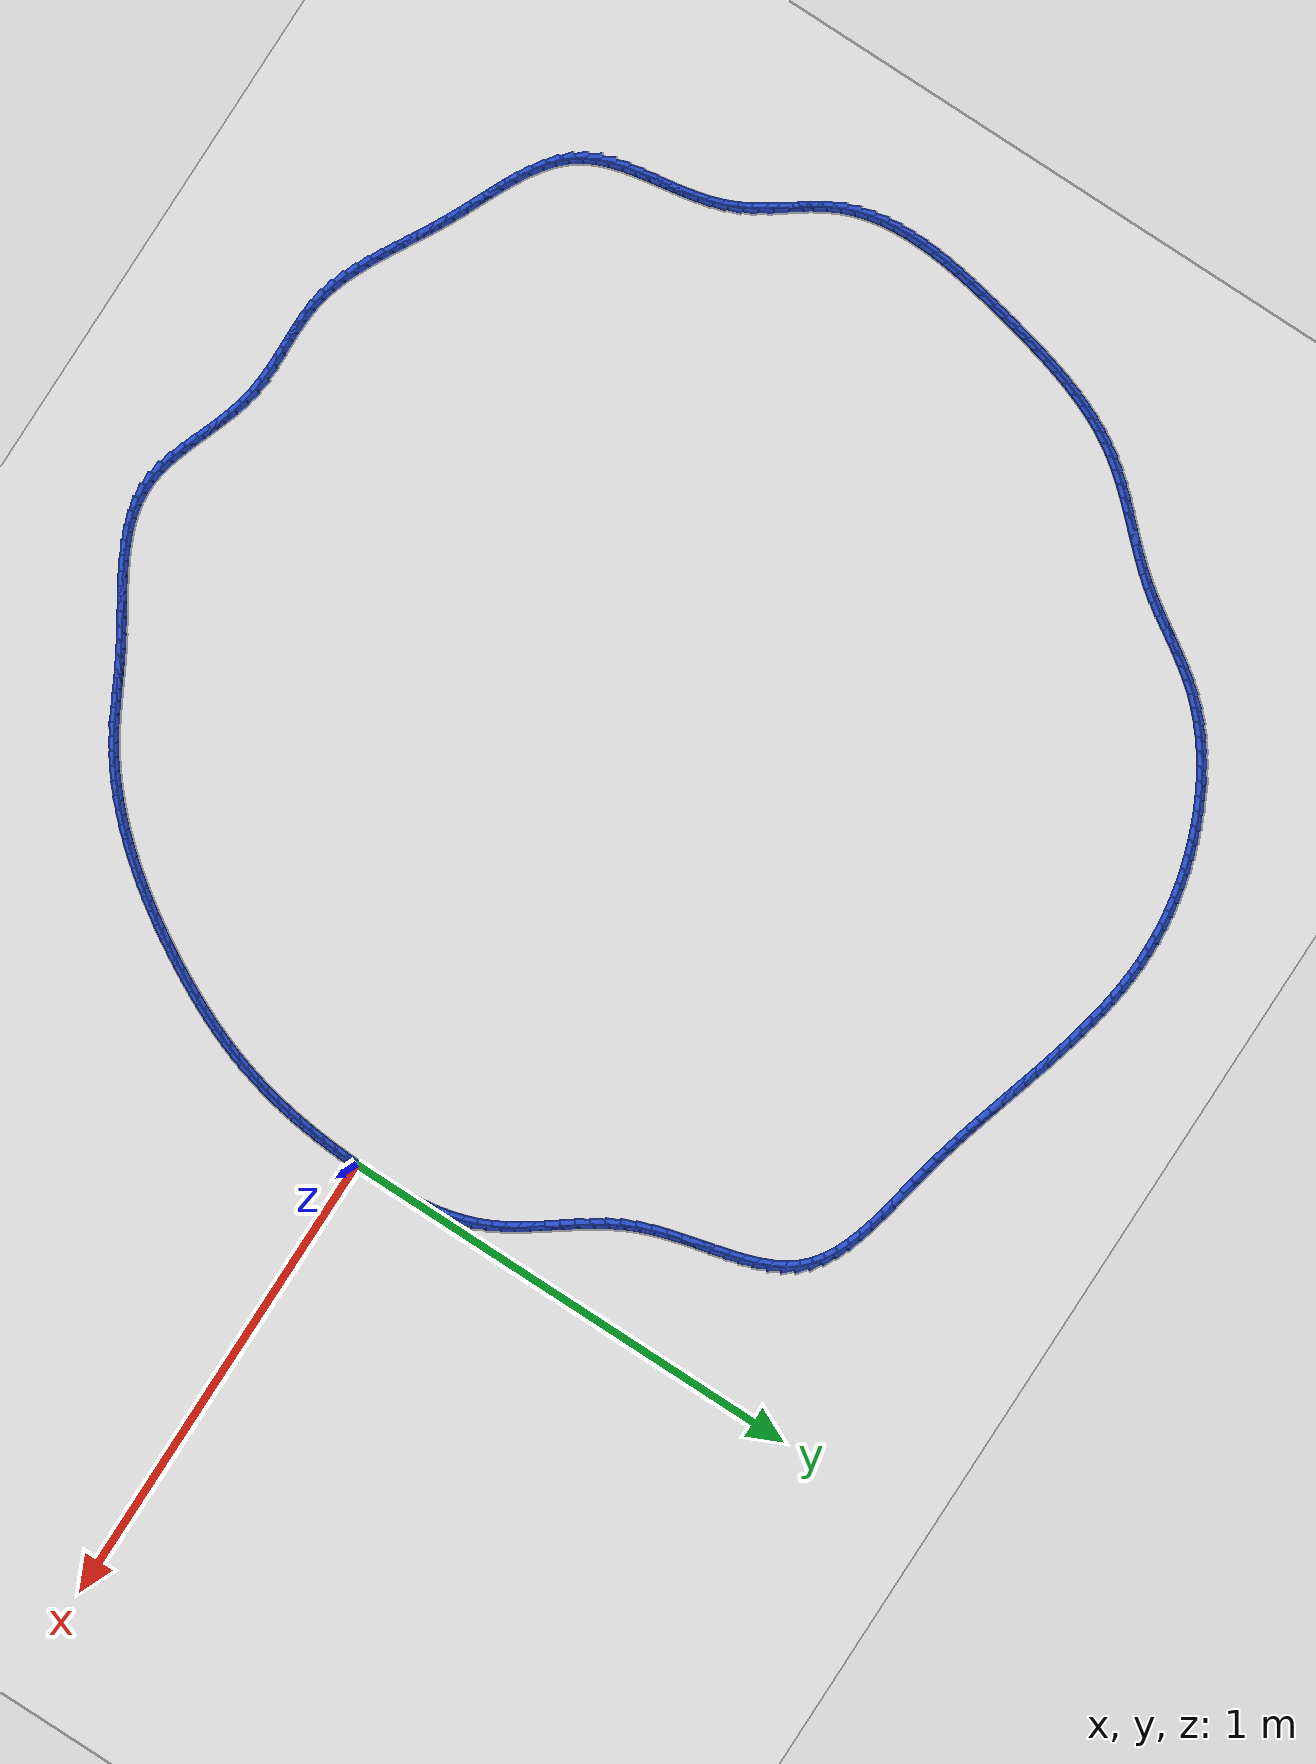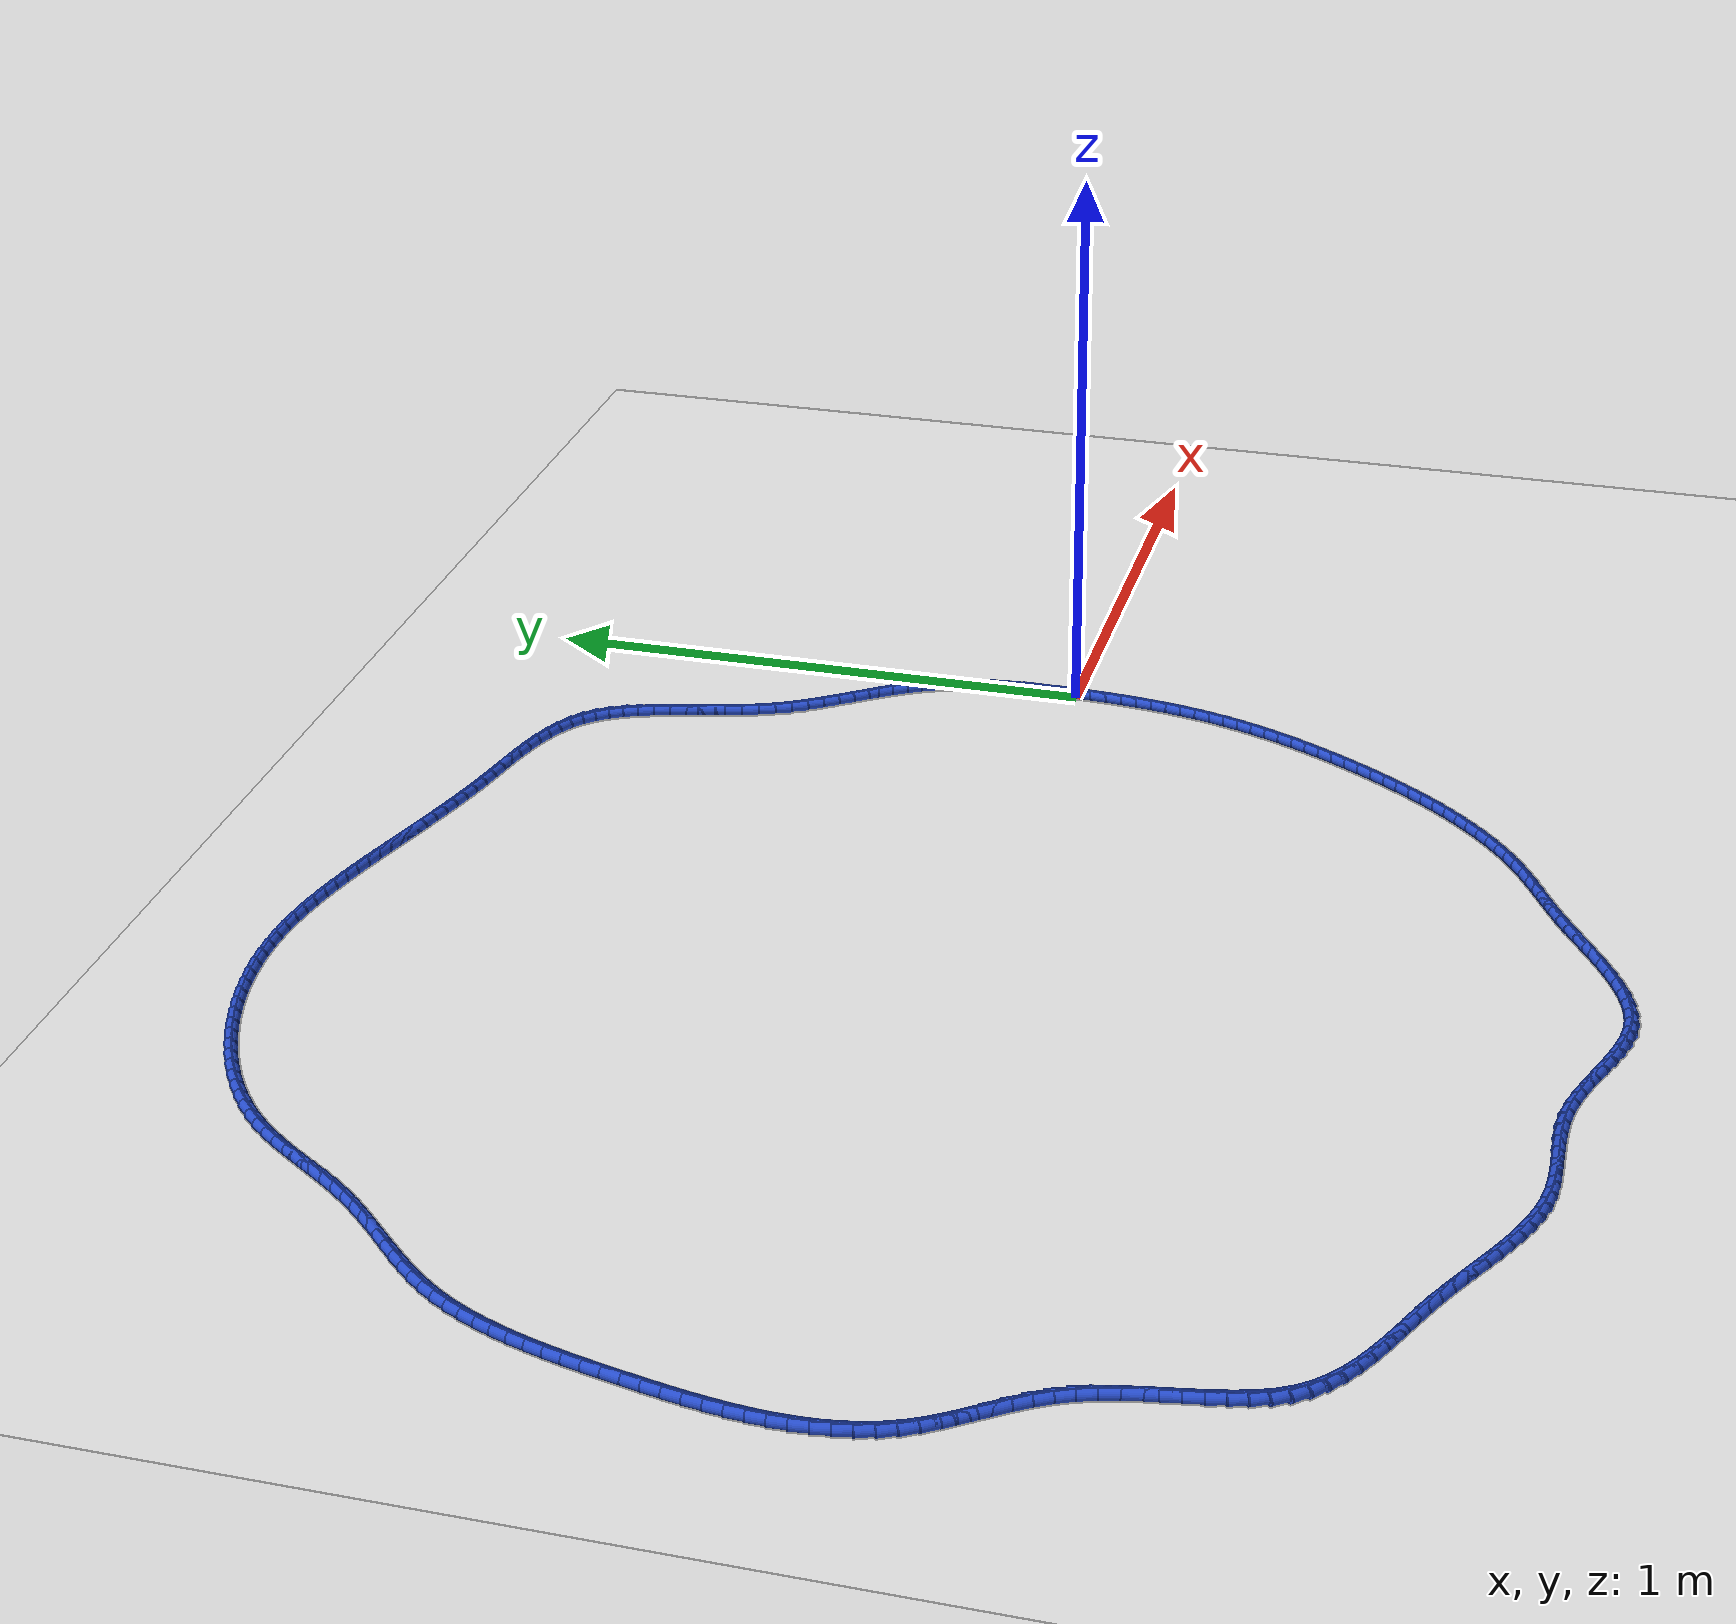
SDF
<sdf version="1.6">
 <world name="default">
  <light name="sun" type="directional">
   <pose>0 0 10 0 -0 0</pose>
   <diffuse>0.8 0.8 0.8 1</diffuse>
   <specular>0.2 0.2 0.2 1</specular>
   <attenuation>
    <range>1000</range>
    <constant>0.9</constant>
    <linear>0.01</linear>
    <quadratic>0.001</quadratic>
   </attenuation>
   <direction>-0.5 0.1 -0.9</direction>
  </light>
  <model name="ground_plane">
   <static>1</static>
   <link name="link">
    <collision name="collision">
     <geometry><plane><normal>0 0 1</normal><size>100 100</size></plane></geometry>
     <surface><friction><ode><mu>100</mu><mu2>50</mu2></ode></friction></surface>
    </collision>
    <visual name="visual">
     <cast_shadows>0</cast_shadows>
     <geometry><plane><normal>0 0 1</normal><size>100 100</size></plane></geometry>
     <material>
      <script><uri>file://media/materials/scripts/gazebo.material</uri><name>Gazebo/WhiteGlow</name></script>
     </material>
    </visual>
   </link>
  </model>
  <gravity>0 0 -9.8</gravity>
  <magnetic_field>6e-06 2.3e-05 -4.2e-05</magnetic_field>
  <atmosphere type="adiabatic"/>
  <physics name="default_physics" default="0" type="ode">
   <max_step_size>0.001</max_step_size>
   <real_time_factor>1</real_time_factor>
   <real_time_update_rate>1000</real_time_update_rate>
  </physics>
  <scene><ambient>0.4 0.4 0.4 1</ambient><background>0.7 0.7 0.7 1</background><shadows>1</shadows></scene>
  <spherical_coordinates>
   <surface_model>EARTH_WGS84</surface_model>
   <latitude_deg>0</latitude_deg>
   <longitude_deg>0</longitude_deg>
   <elevation>0</elevation>
   <heading_deg>0</heading_deg>
  </spherical_coordinates>
  <model name="line">
   <link name="link_0">
    <pose>-5.637851296924623e-18 -8.326672684688674e-17 0.01 0 1.57 1.5493256196764098</pose>
    <collision name="collision">
     <geometry><cylinder><radius>0.01</radius><length>0.08</length></cylinder></geometry>
    </collision>
    <visual name="visual">
     <material>
      <script><name>Gazebo/Blue</name><uri>file://media/materials/scripts/gazebo.material</uri></script>
     </material>
     <geometry><cylinder><radius>0.01</radius><length>0.08</length></cylinder></geometry>
    </visual>
   </link>
   <link name="link_1">
    <pose>0.0006409472577638208 0.02984758540266312 0.01 0 1.57 -1.569960433688251</pose>
    <collision name="collision">
     <geometry><cylinder><radius>0.01</radius><length>0.08</length></cylinder></geometry>
    </collision>
    <visual name="visual">
     <material>
      <script><name>Gazebo/Blue</name><uri>file://media/materials/scripts/gazebo.material</uri></script>
     </material>
     <geometry><cylinder><radius>0.01</radius><length>0.08</length></cylinder></geometry>
    </visual>
   </link>
   <link name="link_2">
    <pose>0.0006159448351102062 0.059758607077116825 0.01 0 1.57 -1.5417701849137226</pose>
    <collision name="collision">
     <geometry><cylinder><radius>0.01</radius><length>0.08</length></cylinder></geometry>
    </collision>
    <visual name="visual">
     <material>
      <script><name>Gazebo/Blue</name><uri>file://media/materials/scripts/gazebo.material</uri></script>
     </material>
     <geometry><cylinder><radius>0.01</radius><length>0.08</length></cylinder></geometry>
    </visual>
   </link>
   <link name="link_3">
    <pose>-0.00025057467721713517 0.089603295005535 0.01 0 1.57 -1.5073506011070712</pose>
    <collision name="collision">
     <geometry><cylinder><radius>0.01</radius><length>0.08</length></cylinder></geometry>
    </collision>
    <visual name="visual">
     <material>
      <script><name>Gazebo/Blue</name><uri>file://media/materials/scripts/gazebo.material</uri></script>
     </material>
     <geometry><cylinder><radius>0.01</radius><length>0.08</length></cylinder></geometry>
    </visual>
   </link>
   <link name="link_4">
    <pose>-0.0021341786884744923 0.11925187917009146 0.01 0 1.57 -1.4662683386564597</pose>
    <collision name="collision">
     <geometry><cylinder><radius>0.01</radius><length>0.08</length></cylinder></geometry>
    </collision>
    <visual name="visual">
     <material>
      <script><name>Gazebo/Blue</name><uri>file://media/materials/scripts/gazebo.material</uri></script>
     </material>
     <geometry><cylinder><radius>0.01</radius><length>0.08</length></cylinder></geometry>
    </visual>
   </link>
   <link name="link_5">
    <pose>-0.005210434607918151 0.14857458955296016 0.01 0 1.57 -1.4180323461217896</pose>
    <collision name="collision">
     <geometry><cylinder><radius>0.01</radius><length>0.08</length></cylinder></geometry>
    </collision>
    <visual name="visual">
     <material>
      <script><name>Gazebo/Blue</name><uri>file://media/materials/scripts/gazebo.material</uri></script>
     </material>
     <geometry><cylinder><radius>0.01</radius><length>0.08</length></cylinder></geometry>
    </visual>
   </link>
   <link name="link_6">
    <pose>-0.009654909844804401 0.17744165613631502 0.01 0 1.57 -1.3621414315614282</pose>
    <collision name="collision">
     <geometry><cylinder><radius>0.01</radius><length>0.08</length></cylinder></geometry>
    </collision>
    <visual name="visual">
     <material>
      <script><name>Gazebo/Blue</name><uri>file://media/materials/scripts/gazebo.material</uri></script>
     </material>
     <geometry><cylinder><radius>0.01</radius><length>0.08</length></cylinder></geometry>
    </visual>
   </link>
   <link name="link_7">
    <pose>-0.015643171808389526 0.20572330890232987 0.01 0 1.57 -1.2981575260807563</pose>
    <collision name="collision">
     <geometry><cylinder><radius>0.01</radius><length>0.08</length></cylinder></geometry>
    </collision>
    <visual name="visual">
     <material>
      <script><name>Gazebo/Blue</name><uri>file://media/materials/scripts/gazebo.material</uri></script>
     </material>
     <geometry><cylinder><radius>0.01</radius><length>0.08</length></cylinder></geometry>
    </visual>
   </link>
   <link name="link_8">
    <pose>-0.02335078790792982 0.23328977783317867 0.01 0 1.57 -1.2258109475852548</pose>
    <collision name="collision">
     <geometry><cylinder><radius>0.01</radius><length>0.08</length></cylinder></geometry>
    </collision>
    <visual name="visual">
     <material>
      <script><name>Gazebo/Blue</name><uri>file://media/materials/scripts/gazebo.material</uri></script>
     </material>
     <geometry><cylinder><radius>0.01</radius><length>0.08</length></cylinder></geometry>
    </visual>
   </link>
   <link name="link_9">
    <pose>-0.03295332555268156 0.2600112929110353 0.01 0 1.57 -1.1460980289142053</pose>
    <collision name="collision">
     <geometry><cylinder><radius>0.01</radius><length>0.08</length></cylinder></geometry>
    </collision>
    <visual name="visual">
     <material>
      <script><name>Gazebo/Blue</name><uri>file://media/materials/scripts/gazebo.material</uri></script>
     </material>
     <geometry><cylinder><radius>0.01</radius><length>0.08</length></cylinder></geometry>
    </visual>
   </link>
   <link name="link_10">
    <pose>-0.04460309304341617 0.28577259310153785 0.01 0 1.57 -1.0726730290716613</pose>
    <collision name="collision">
     <geometry><cylinder><radius>0.01</radius><length>0.08</length></cylinder></geometry>
    </collision>
    <visual name="visual">
     <material>
      <script><name>Gazebo/Blue</name><uri>file://media/materials/scripts/gazebo.material</uri></script>
     </material>
     <geometry><cylinder><radius>0.01</radius><length>0.08</length></cylinder></geometry>
    </visual>
   </link>
   <link name="link_11">
    <pose>-0.0581362016974307 0.3106556603905201 0.01 0 1.57 -1.0157282815609903</pose>
    <collision name="collision">
     <geometry><cylinder><radius>0.01</radius><length>0.08</length></cylinder></geometry>
    </collision>
    <visual name="visual">
     <material>
      <script><name>Gazebo/Blue</name><uri>file://media/materials/scripts/gazebo.material</uri></script>
     </material>
     <geometry><cylinder><radius>0.01</radius><length>0.08</length></cylinder></geometry>
    </visual>
   </link>
   <link name="link_12">
    <pose>-0.07316066976703656 0.3348847607430282 0.01 0 1.57 -0.9755450756221523</pose>
    <collision name="collision">
     <geometry><cylinder><radius>0.01</radius><length>0.08</length></cylinder></geometry>
    </collision>
    <visual name="visual">
     <material>
      <script><name>Gazebo/Blue</name><uri>file://media/materials/scripts/gazebo.material</uri></script>
     </material>
     <geometry><cylinder><radius>0.01</radius><length>0.08</length></cylinder></geometry>
    </visual>
   </link>
   <link name="link_13">
    <pose>-0.08927946854012592 0.35868730841000834 0.01 0 1.57 -0.9517676002454188</pose>
    <collision name="collision">
     <geometry><cylinder><radius>0.01</radius><length>0.08</length></cylinder></geometry>
    </collision>
    <visual name="visual">
     <material>
      <script><name>Gazebo/Blue</name><uri>file://media/materials/scripts/gazebo.material</uri></script>
     </material>
     <geometry><cylinder><radius>0.01</radius><length>0.08</length></cylinder></geometry>
    </visual>
   </link>
   <link name="link_14">
    <pose>-0.10609556930459092 0.3822907176424073 0.01 0 1.57 -0.9439486541926309</pose>
    <collision name="collision">
     <geometry><cylinder><radius>0.01</radius><length>0.08</length></cylinder></geometry>
    </collision>
    <visual name="visual">
     <material>
      <script><name>Gazebo/Blue</name><uri>file://media/materials/scripts/gazebo.material</uri></script>
     </material>
     <geometry><cylinder><radius>0.01</radius><length>0.08</length></cylinder></geometry>
    </visual>
   </link>
   <link name="link_15">
    <pose>-0.12321194334832368 0.4059224026911712 0.01 0 1.57 -0.9517340529604628</pose>
    <collision name="collision">
     <geometry><cylinder><radius>0.01</radius><length>0.08</length></cylinder></geometry>
    </collision>
    <visual name="visual">
     <material>
      <script><name>Gazebo/Blue</name><uri>file://media/materials/scripts/gazebo.material</uri></script>
     </material>
     <geometry><cylinder><radius>0.01</radius><length>0.08</length></cylinder></geometry>
    </visual>
   </link>
   <link name="link_16">
    <pose>-0.1402315619592165 0.4298097778072469 0.01 0 1.57 -0.9749140818394112</pose>
    <collision name="collision">
     <geometry><cylinder><radius>0.01</radius><length>0.08</length></cylinder></geometry>
    </collision>
    <visual name="visual">
     <material>
      <script><name>Gazebo/Blue</name><uri>file://media/materials/scripts/gazebo.material</uri></script>
     </material>
     <geometry><cylinder><radius>0.01</radius><length>0.08</length></cylinder></geometry>
    </visual>
   </link>
   <link name="link_17">
    <pose>-0.15675739642516137 0.45418025724158056 0.01 0 1.57 -1.0133619687625222</pose>
    <collision name="collision">
     <geometry><cylinder><radius>0.01</radius><length>0.08</length></cylinder></geometry>
    </collision>
    <visual name="visual">
     <material>
      <script><name>Gazebo/Blue</name><uri>file://media/materials/scripts/gazebo.material</uri></script>
     </material>
     <geometry><cylinder><radius>0.01</radius><length>0.08</length></cylinder></geometry>
    </visual>
   </link>
   <link name="link_18">
    <pose>-0.17239241803405053 0.4792612552451187 0.01 0 1.57 -1.0668688279705607</pose>
    <collision name="collision">
     <geometry><cylinder><radius>0.01</radius><length>0.08</length></cylinder></geometry>
    </collision>
    <visual name="visual">
     <material>
      <script><name>Gazebo/Blue</name><uri>file://media/materials/scripts/gazebo.material</uri></script>
     </material>
     <geometry><cylinder><radius>0.01</radius><length>0.08</length></cylinder></geometry>
    </visual>
   </link>
   <link name="link_19">
    <pose>-0.1867395980737762 0.5052801860688079 0.01 0 1.57 -1.134840986003388</pose>
    <collision name="collision">
     <geometry><cylinder><radius>0.01</radius><length>0.08</length></cylinder></geometry>
    </collision>
    <visual name="visual">
     <material>
      <script><name>Gazebo/Blue</name><uri>file://media/materials/scripts/gazebo.material</uri></script>
     </material>
     <geometry><cylinder><radius>0.01</radius><length>0.08</length></cylinder></geometry>
    </visual>
   </link>
   <link name="link_20">
    <pose>-0.1994030000032319 0.5324636885692487 0.01 0 1.57 -1.2069468422055816</pose>
    <collision name="collision">
     <geometry><cylinder><radius>0.01</radius><length>0.08</length></cylinder></geometry>
    </collision>
    <visual name="visual">
     <material>
      <script><name>Gazebo/Blue</name><uri>file://media/materials/scripts/gazebo.material</uri></script>
     </material>
     <geometry><cylinder><radius>0.01</radius><length>0.08</length></cylinder></geometry>
    </visual>
   </link>
   <link name="link_21">
    <pose>-0.21022101664508128 0.5608720378528336 0.01 0 1.57 -1.2625666835470688</pose>
    <collision name="collision">
     <geometry><cylinder><radius>0.01</radius><length>0.08</length></cylinder></geometry>
    </collision>
    <visual name="visual">
     <material>
      <script><name>Gazebo/Blue</name><uri>file://media/materials/scripts/gazebo.material</uri></script>
     </material>
     <geometry><cylinder><radius>0.01</radius><length>0.08</length></cylinder></geometry>
    </visual>
   </link>
   <link name="link_22">
    <pose>-0.2195562369697719 0.5901933523504638 0.01 0 1.57 -1.3002098207081696</pose>
    <collision name="collision">
     <geometry><cylinder><radius>0.01</radius><length>0.08</length></cylinder></geometry>
    </collision>
    <visual name="visual">
     <material>
      <script><name>Gazebo/Blue</name><uri>file://media/materials/scripts/gazebo.material</uri></script>
     </material>
     <geometry><cylinder><radius>0.01</radius><length>0.08</length></cylinder></geometry>
    </visual>
   </link>
   <link name="link_23">
    <pose>-0.22784239092838027 0.620065243462506 0.01 0 1.57 -1.320945639653934</pose>
    <collision name="collision">
     <geometry><cylinder><radius>0.01</radius><length>0.08</length></cylinder></geometry>
    </collision>
    <visual name="visual">
     <material>
      <script><name>Gazebo/Blue</name><uri>file://media/materials/scripts/gazebo.material</uri></script>
     </material>
     <geometry><cylinder><radius>0.01</radius><length>0.08</length></cylinder></geometry>
    </visual>
   </link>
   <link name="link_24">
    <pose>-0.23551320847198332 0.650125322589328 0.01 0 1.57 -1.3252590220329108</pose>
    <collision name="collision">
     <geometry><cylinder><radius>0.01</radius><length>0.08</length></cylinder></geometry>
    </collision>
    <visual name="visual">
     <material>
      <script><name>Gazebo/Blue</name><uri>file://media/materials/scripts/gazebo.material</uri></script>
     </material>
     <geometry><cylinder><radius>0.01</radius><length>0.08</length></cylinder></geometry>
    </visual>
   </link>
   <link name="link_25">
    <pose>-0.24300241955165755 0.6800112011312963 0.01 0 1.57 -1.3129042982043717</pose>
    <collision name="collision">
     <geometry><cylinder><radius>0.01</radius><length>0.08</length></cylinder></geometry>
    </collision>
    <visual name="visual">
     <material>
      <script><name>Gazebo/Blue</name><uri>file://media/materials/scripts/gazebo.material</uri></script>
     </material>
     <geometry><cylinder><radius>0.01</radius><length>0.08</length></cylinder></geometry>
    </visual>
   </link>
   <link name="link_26">
    <pose>-0.2507437541184798 0.7093604904887786 0.01 0 1.57 -1.282822759139228</pose>
    <collision name="collision">
     <geometry><cylinder><radius>0.01</radius><length>0.08</length></cylinder></geometry>
    </collision>
    <visual name="visual">
     <material>
      <script><name>Gazebo/Blue</name><uri>file://media/materials/scripts/gazebo.material</uri></script>
     </material>
     <geometry><cylinder><radius>0.01</radius><length>0.08</length></cylinder></geometry>
    </visual>
   </link>
   <link name="link_27">
    <pose>-0.25917094212352665 0.7378108020621414 0.01 0 1.57 -1.2331178961608336</pose>
    <collision name="collision">
     <geometry><cylinder><radius>0.01</radius><length>0.08</length></cylinder></geometry>
    </collision>
    <visual name="visual">
     <material>
      <script><name>Gazebo/Blue</name><uri>file://media/materials/scripts/gazebo.material</uri></script>
     </material>
     <geometry><cylinder><radius>0.01</radius><length>0.08</length></cylinder></geometry>
    </visual>
   </link>
   <link name="link_28">
    <pose>-0.268717713517875 0.7649997472517527 0.01 0 1.57 -1.1611696343551625</pose>
    <collision name="collision">
     <geometry><cylinder><radius>0.01</radius><length>0.08</length></cylinder></geometry>
    </collision>
    <visual name="visual">
     <material>
      <script><name>Gazebo/Blue</name><uri>file://media/materials/scripts/gazebo.material</uri></script>
     </material>
     <geometry><cylinder><radius>0.01</radius><length>0.08</length></cylinder></geometry>
    </visual>
   </link>
   <link name="link_29">
    <pose>-0.27981779825260134 0.7905649374579788 0.01 0 1.57 -1.0640979018220516</pose>
    <collision name="collision">
     <geometry><cylinder><radius>0.01</radius><length>0.08</length></cylinder></geometry>
    </collision>
    <visual name="visual">
     <material>
      <script><name>Gazebo/Blue</name><uri>file://media/materials/scripts/gazebo.material</uri></script>
     </material>
     <geometry><cylinder><radius>0.01</radius><length>0.08</length></cylinder></geometry>
    </visual>
   </link>
   <link name="link_30">
    <pose>-0.2929049262787825 0.8141439840811872 0.01 0 1.57 -0.9399228599757675</pose>
    <collision name="collision">
     <geometry><cylinder><radius>0.01</radius><length>0.08</length></cylinder></geometry>
    </collision>
    <visual name="visual">
     <material>
      <script><name>Gazebo/Blue</name><uri>file://media/materials/scripts/gazebo.material</uri></script>
     </material>
     <geometry><cylinder><radius>0.01</radius><length>0.08</length></cylinder></geometry>
    </visual>
   </link>
   <link name="link_31">
    <pose>-0.3084128275474951 0.8353744985217452 0.01 0 1.57 -0.7903698727182531</pose>
    <collision name="collision">
     <geometry><cylinder><radius>0.01</radius><length>0.08</length></cylinder></geometry>
    </collision>
    <visual name="visual">
     <material>
      <script><name>Gazebo/Blue</name><uri>file://media/materials/scripts/gazebo.material</uri></script>
     </material>
     <geometry><cylinder><radius>0.01</radius><length>0.08</length></cylinder></geometry>
    </visual>
   </link>
   <link name="link_32">
    <pose>-0.3267611357591894 0.8539061647568917 0.01 0 1.57 -0.6399078186234167</pose>
    <collision name="collision">
     <geometry><cylinder><radius>0.01</radius><length>0.08</length></cylinder></geometry>
    </collision>
    <visual name="visual">
     <material>
      <script><name>Gazebo/Blue</name><uri>file://media/materials/scripts/gazebo.material</uri></script>
     </material>
     <geometry><cylinder><radius>0.01</radius><length>0.08</length></cylinder></geometry>
    </visual>
   </link>
   <link name="link_33">
    <pose>-0.34799295417193726 0.8697111420681786 0.01 0 1.57 -0.5136813415873034</pose>
    <collision name="collision">
     <geometry><cylinder><radius>0.01</radius><length>0.08</length></cylinder></geometry>
    </collision>
    <visual name="visual">
     <material>
      <script><name>Gazebo/Blue</name><uri>file://media/materials/scripts/gazebo.material</uri></script>
     </material>
     <geometry><cylinder><radius>0.01</radius><length>0.08</length></cylinder></geometry>
    </visual>
   </link>
   <link name="link_34">
    <pose>-0.3717432709224275 0.8831111153880724 0.01 0 1.57 -0.4127401987999664</pose>
    <collision name="collision">
     <geometry><cylinder><radius>0.01</radius><length>0.08</length></cylinder></geometry>
    </collision>
    <visual name="visual">
     <material>
      <script><name>Gazebo/Blue</name><uri>file://media/materials/scripts/gazebo.material</uri></script>
     </material>
     <geometry><cylinder><radius>0.01</radius><length>0.08</length></cylinder></geometry>
    </visual>
   </link>
   <link name="link_35">
    <pose>-0.3976266481096563 0.8944452633015562 0.01 0 1.57 -0.33463089188393325</pose>
    <collision name="collision">
     <geometry><cylinder><radius>0.01</radius><length>0.08</length></cylinder></geometry>
    </collision>
    <visual name="visual">
     <material>
      <script><name>Gazebo/Blue</name><uri>file://media/materials/scripts/gazebo.material</uri></script>
     </material>
     <geometry><cylinder><radius>0.01</radius><length>0.08</length></cylinder></geometry>
    </visual>
   </link>
   <link name="link_36">
    <pose>-0.42525764783262 0.9040527643936135 0.01 0 1.57 -0.2762661418907046</pose>
    <collision name="collision">
     <geometry><cylinder><radius>0.01</radius><length>0.08</length></cylinder></geometry>
    </collision>
    <visual name="visual">
     <material>
      <script><name>Gazebo/Blue</name><uri>file://media/materials/scripts/gazebo.material</uri></script>
     </material>
     <geometry><cylinder><radius>0.01</radius><length>0.08</length></cylinder></geometry>
    </visual>
   </link>
   <link name="link_37">
    <pose>-0.4542508321903152 0.9122727972492278 0.01 0 1.57 -0.2348810649256387</pose>
    <collision name="collision">
     <geometry><cylinder><radius>0.01</radius><length>0.08</length></cylinder></geometry>
    </collision>
    <visual name="visual">
     <material>
      <script><name>Gazebo/Blue</name><uri>file://media/materials/scripts/gazebo.material</uri></script>
     </material>
     <geometry><cylinder><radius>0.01</radius><length>0.08</length></cylinder></geometry>
    </visual>
   </link>
   <link name="link_38">
    <pose>-0.4842207632817376 0.9194445404533822 0.01 0 1.57 -0.20839488779222015</pose>
    <collision name="collision">
     <geometry><cylinder><radius>0.01</radius><length>0.08</length></cylinder></geometry>
    </collision>
    <visual name="visual">
     <material>
      <script><name>Gazebo/Blue</name><uri>file://media/materials/scripts/gazebo.material</uri></script>
     </material>
     <geometry><cylinder><radius>0.01</radius><length>0.08</length></cylinder></geometry>
    </visual>
   </link>
   <link name="link_39">
    <pose>-0.5147820032058843 0.9259071725910604 0.01 0 1.57 -0.19549713225670143</pose>
    <collision name="collision">
     <geometry><cylinder><radius>0.01</radius><length>0.08</length></cylinder></geometry>
    </collision>
    <visual name="visual">
     <material>
      <script><name>Gazebo/Blue</name><uri>file://media/materials/scripts/gazebo.material</uri></script>
     </material>
     <geometry><cylinder><radius>0.01</radius><length>0.08</length></cylinder></geometry>
    </visual>
   </link>
   <link name="link_40">
    <pose>-0.545549114061751 0.9319998722472451 0.01 0 1.57 -0.19564829324302893</pose>
    <collision name="collision">
     <geometry><cylinder><radius>0.01</radius><length>0.08</length></cylinder></geometry>
    </collision>
    <visual name="visual">
     <material>
      <script><name>Gazebo/Blue</name><uri>file://media/materials/scripts/gazebo.material</uri></script>
     </material>
     <geometry><cylinder><radius>0.01</radius><length>0.08</length></cylinder></geometry>
    </visual>
   </link>
   <link name="link_41">
    <pose>-0.5761366579483342 0.9380618180069199 0.01 0 1.57 -0.20856050098652676</pose>
    <collision name="collision">
     <geometry><cylinder><radius>0.01</radius><length>0.08</length></cylinder></geometry>
    </collision>
    <visual name="visual">
     <material>
      <script><name>Gazebo/Blue</name><uri>file://media/materials/scripts/gazebo.material</uri></script>
     </material>
     <geometry><cylinder><radius>0.01</radius><length>0.08</length></cylinder></geometry>
    </visual>
   </link>
   <link name="link_42">
    <pose>-0.6061750873740807 0.9444190914313313 0.01 0 1.57 -0.22650400562591008</pose>
    <collision name="collision">
     <geometry><cylinder><radius>0.01</radius><length>0.08</length></cylinder></geometry>
    </collision>
    <visual name="visual">
     <material>
      <script><name>Gazebo/Blue</name><uri>file://media/materials/scripts/gazebo.material</uri></script>
     </material>
     <geometry><cylinder><radius>0.01</radius><length>0.08</length></cylinder></geometry>
    </visual>
   </link>
   <link name="link_43">
    <pose>-0.6355487533799522 0.9511885085421774 0.01 0 1.57 -0.24271823996712683</pose>
    <collision name="collision">
     <geometry><cylinder><radius>0.01</radius><length>0.08</length></cylinder></geometry>
    </collision>
    <visual name="visual">
     <material>
      <script><name>Gazebo/Blue</name><uri>file://media/materials/scripts/gazebo.material</uri></script>
     </material>
     <geometry><cylinder><radius>0.01</radius><length>0.08</length></cylinder></geometry>
    </visual>
   </link>
   <link name="link_44">
    <pose>-0.6643460519003547 0.9583187096561026 0.01 0 1.57 -0.25677958658338</pose>
    <collision name="collision">
     <geometry><cylinder><radius>0.01</radius><length>0.08</length></cylinder></geometry>
    </collision>
    <visual name="visual">
     <material>
      <script><name>Gazebo/Blue</name><uri>file://media/materials/scripts/gazebo.material</uri></script>
     </material>
     <geometry><cylinder><radius>0.01</radius><length>0.08</length></cylinder></geometry>
    </visual>
   </link>
   <link name="link_45">
    <pose>-0.6926611489610266 0.9657535793266353 0.01 0 1.57 -0.26848208417424424</pose>
    <collision name="collision">
     <geometry><cylinder><radius>0.01</radius><length>0.08</length></cylinder></geometry>
    </collision>
    <visual name="visual">
     <material>
      <script><name>Gazebo/Blue</name><uri>file://media/materials/scripts/gazebo.material</uri></script>
     </material>
     <geometry><cylinder><radius>0.01</radius><length>0.08</length></cylinder></geometry>
    </visual>
   </link>
   <link name="link_46">
    <pose>-0.7205882105877066 0.9734370021073038 0.01 0 1.57 -0.27765256714027803</pose>
    <collision name="collision">
     <geometry><cylinder><radius>0.01</radius><length>0.08</length></cylinder></geometry>
    </collision>
    <visual name="visual">
     <material>
      <script><name>Gazebo/Blue</name><uri>file://media/materials/scripts/gazebo.material</uri></script>
     </material>
     <geometry><cylinder><radius>0.01</radius><length>0.08</length></cylinder></geometry>
    </visual>
   </link>
   <link name="link_47">
    <pose>-0.7482214028061333 0.9813128625516364 0.01 0 1.57 -0.2841551532694134</pose>
    <collision name="collision">
     <geometry><cylinder><radius>0.01</radius><length>0.08</length></cylinder></geometry>
    </collision>
    <visual name="visual">
     <material>
      <script><name>Gazebo/Blue</name><uri>file://media/materials/scripts/gazebo.material</uri></script>
     </material>
     <geometry><cylinder><radius>0.01</radius><length>0.08</length></cylinder></geometry>
    </visual>
   </link>
   <link name="link_48">
    <pose>-0.7756548916420453 0.989325045213162 0.01 0 1.57 -0.28789459711574855</pose>
    <collision name="collision">
     <geometry><cylinder><radius>0.01</radius><length>0.08</length></cylinder></geometry>
    </collision>
    <visual name="visual">
     <material>
      <script><name>Gazebo/Blue</name><uri>file://media/materials/scripts/gazebo.material</uri></script>
     </material>
     <geometry><cylinder><radius>0.01</radius><length>0.08</length></cylinder></geometry>
    </visual>
   </link>
   <link name="link_49">
    <pose>-0.8029828431211806 0.9974174346454079 0.01 0 1.57 -0.2888185059375868</pose>
    <collision name="collision">
     <geometry><cylinder><radius>0.01</radius><length>0.08</length></cylinder></geometry>
    </collision>
    <visual name="visual">
     <material>
      <script><name>Gazebo/Blue</name><uri>file://media/materials/scripts/gazebo.material</uri></script>
     </material>
     <geometry><cylinder><radius>0.01</radius><length>0.08</length></cylinder></geometry>
    </visual>
   </link>
   <link name="link_50">
    <pose>-0.8302994232692786 1.0055339154019034 0.01 0 1.57 -0.2869184475515514</pose>
    <collision name="collision">
     <geometry><cylinder><radius>0.01</radius><length>0.08</length></cylinder></geometry>
    </collision>
    <visual name="visual">
     <material>
      <script><name>Gazebo/Blue</name><uri>file://media/materials/scripts/gazebo.material</uri></script>
     </material>
     <geometry><cylinder><radius>0.01</radius><length>0.08</length></cylinder></geometry>
    </visual>
   </link>
   <link name="link_51">
    <pose>-0.8576987981120779 1.0136183720361764 0.01 0 1.57 -0.28222971263009006</pose>
    <collision name="collision">
     <geometry><cylinder><radius>0.01</radius><length>0.08</length></cylinder></geometry>
    </collision>
    <visual name="visual">
     <material>
      <script><name>Gazebo/Blue</name><uri>file://media/materials/scripts/gazebo.material</uri></script>
     </material>
     <geometry><cylinder><radius>0.01</radius><length>0.08</length></cylinder></geometry>
    </visual>
   </link>
   <link name="link_52">
    <pose>-0.8852750954974394 1.0216146699006705 0.01 0 1.57 -0.27462542555345076</pose>
    <collision name="collision">
     <geometry><cylinder><radius>0.01</radius><length>0.08</length></cylinder></geometry>
    </collision>
    <visual name="visual">
     <material>
      <script><name>Gazebo/Blue</name><uri>file://media/materials/scripts/gazebo.material</uri></script>
     </material>
     <geometry><cylinder><radius>0.01</radius><length>0.08</length></cylinder></geometry>
    </visual>
   </link>
   <link name="link_53">
    <pose>-0.9130945313568064 1.0294526363991656 0.01 0 1.57 -0.2636023882718563</pose>
    <collision name="collision">
     <geometry><cylinder><radius>0.01</radius><length>0.08</length></cylinder></geometry>
    </collision>
    <visual name="visual">
     <material>
      <script><name>Gazebo/Blue</name><uri>file://media/materials/scripts/gazebo.material</uri></script>
     </material>
     <geometry><cylinder><radius>0.01</radius><length>0.08</length></cylinder></geometry>
    </visual>
   </link>
   <link name="link_54">
    <pose>-0.941146120559467 1.0370232716284578 0.01 0 1.57 -0.24906318397910146</pose>
    <collision name="collision">
     <geometry><cylinder><radius>0.01</radius><length>0.08</length></cylinder></geometry>
    </collision>
    <visual name="visual">
     <material>
      <script><name>Gazebo/Blue</name><uri>file://media/materials/scripts/gazebo.material</uri></script>
     </material>
     <geometry><cylinder><radius>0.01</radius><length>0.08</length></cylinder></geometry>
    </visual>
   </link>
   <link name="link_55">
    <pose>-0.9694056419272024 1.0442109187810804 0.01 0 1.57 -0.23097330110745212</pose>
    <collision name="collision">
     <geometry><cylinder><radius>0.01</radius><length>0.08</length></cylinder></geometry>
    </collision>
    <visual name="visual">
     <material>
      <script><name>Gazebo/Blue</name><uri>file://media/materials/scripts/gazebo.material</uri></script>
     </material>
     <geometry><cylinder><radius>0.01</radius><length>0.08</length></cylinder></geometry>
    </visual>
   </link>
   <link name="link_56">
    <pose>-0.9978488742817935 1.0508999210495658 0.01 0 1.57 -0.20927239608331416</pose>
    <collision name="collision">
     <geometry><cylinder><radius>0.01</radius><length>0.08</length></cylinder></geometry>
    </collision>
    <visual name="visual">
     <material>
      <script><name>Gazebo/Blue</name><uri>file://media/materials/scripts/gazebo.material</uri></script>
     </material>
     <geometry><cylinder><radius>0.01</radius><length>0.08</length></cylinder></geometry>
    </visual>
   </link>
   <link name="link_57">
    <pose>-1.0264515964450216 1.0569746216264468 0.01 0 1.57 -0.18388086949557483</pose>
    <collision name="collision">
     <geometry><cylinder><radius>0.01</radius><length>0.08</length></cylinder></geometry>
    </collision>
    <visual name="visual">
     <material>
      <script><name>Gazebo/Blue</name><uri>file://media/materials/scripts/gazebo.material</uri></script>
     </material>
     <geometry><cylinder><radius>0.01</radius><length>0.08</length></cylinder></geometry>
    </visual>
   </link>
   <link name="link_58">
    <pose>-1.0551895872386674 1.0623193637042565 0.01 0 1.57 -0.15470791386955415</pose>
    <collision name="collision">
     <geometry><cylinder><radius>0.01</radius><length>0.08</length></cylinder></geometry>
    </collision>
    <visual name="visual">
     <material>
      <script><name>Gazebo/Blue</name><uri>file://media/materials/scripts/gazebo.material</uri></script>
     </material>
     <geometry><cylinder><radius>0.01</radius><length>0.08</length></cylinder></geometry>
    </visual>
   </link>
   <link name="link_59">
    <pose>-1.084038625484513 1.0668184904755276 0.01 0 1.57 -0.12166155194188981</pose>
    <collision name="collision">
     <geometry><cylinder><radius>0.01</radius><length>0.08</length></cylinder></geometry>
    </collision>
    <visual name="visual">
     <material>
      <script><name>Gazebo/Blue</name><uri>file://media/materials/scripts/gazebo.material</uri></script>
     </material>
     <geometry><cylinder><radius>0.01</radius><length>0.08</length></cylinder></geometry>
    </visual>
   </link>
   <link name="link_60">
    <pose>-1.1129744900043381 1.070356345132792 0.01 0 1.57 -0.08466113518458541</pose>
    <collision name="collision">
     <geometry><cylinder><radius>0.01</radius><length>0.08</length></cylinder></geometry>
    </collision>
    <visual name="visual">
     <material>
      <script><name>Gazebo/Blue</name><uri>file://media/materials/scripts/gazebo.material</uri></script>
     </material>
     <geometry><cylinder><radius>0.01</radius><length>0.08</length></cylinder></geometry>
    </visual>
   </link>
   <link name="link_61">
    <pose>-1.141972959619925 1.0728172708685835 0.01 0 1.57 -0.04365264407227953</pose>
    <collision name="collision">
     <geometry><cylinder><radius>0.01</radius><length>0.08</length></cylinder></geometry>
    </collision>
    <visual name="visual">
     <material>
      <script><name>Gazebo/Blue</name><uri>file://media/materials/scripts/gazebo.material</uri></script>
     </material>
     <geometry><cylinder><radius>0.01</radius><length>0.08</length></cylinder></geometry>
    </visual>
   </link>
   <link name="link_62">
    <pose>-1.171009813053154 1.0740856120294227 0.01 0 1.57 0.0005040791827742568</pose>
    <collision name="collision">
     <geometry><cylinder><radius>0.01</radius><length>0.08</length></cylinder></geometry>
    </collision>
    <visual name="visual">
     <material>
      <script><name>Gazebo/Blue</name><uri>file://media/materials/scripts/gazebo.material</uri></script>
     </material>
     <geometry><cylinder><radius>0.01</radius><length>0.08</length></cylinder></geometry>
    </visual>
   </link>
   <link name="link_63">
    <pose>-1.2000586426086244 1.0740709691179195 0.01 0 1.57 0.04467481798325068</pose>
    <collision name="collision">
     <geometry><cylinder><radius>0.01</radius><length>0.08</length></cylinder></geometry>
    </collision>
    <visual name="visual">
     <material>
      <script><name>Gazebo/Blue</name><uri>file://media/materials/scripts/gazebo.material</uri></script>
     </material>
     <geometry><cylinder><radius>0.01</radius><length>0.08</length></cylinder></geometry>
    </visual>
   </link>
   <link name="link_64">
    <pose>-1.2290852141479631 1.0727733489223477 0.01 0 1.57 0.08815606338495383</pose>
    <collision name="collision">
     <geometry><cylinder><radius>0.01</radius><length>0.08</length></cylinder></geometry>
    </collision>
    <visual name="visual">
     <material>
      <script><name>Gazebo/Blue</name><uri>file://media/materials/scripts/gazebo.material</uri></script>
     </material>
     <geometry><cylinder><radius>0.01</radius><length>0.08</length></cylinder></geometry>
    </visual>
   </link>
   <link name="link_65">
    <pose>-1.2580535430259903 1.0702129790157138 0.01 0 1.57 0.1309522715924106</pose>
    <collision name="collision">
     <geometry><cylinder><radius>0.01</radius><length>0.08</length></cylinder></geometry>
    </collision>
    <visual name="visual">
     <material>
      <script><name>Gazebo/Blue</name><uri>file://media/materials/scripts/gazebo.material</uri></script>
     </material>
     <geometry><cylinder><radius>0.01</radius><length>0.08</length></cylinder></geometry>
    </visual>
   </link>
   <link name="link_66">
    <pose>-1.2869276445975248 1.0664100869710242 0.01 0 1.57 0.17307708043567815</pose>
    <collision name="collision">
     <geometry><cylinder><radius>0.01</radius><length>0.08</length></cylinder></geometry>
    </collision>
    <visual name="visual">
     <material>
      <script><name>Gazebo/Blue</name><uri>file://media/materials/scripts/gazebo.material</uri></script>
     </material>
     <geometry><cylinder><radius>0.01</radius><length>0.08</length></cylinder></geometry>
    </visual>
   </link>
   <link name="link_67">
    <pose>-1.3156715342173853 1.061384900361285 0.01 0 1.57 0.21455219473750126</pose>
    <collision name="collision">
     <geometry><cylinder><radius>0.01</radius><length>0.08</length></cylinder></geometry>
    </collision>
    <visual name="visual">
     <material>
      <script><name>Gazebo/Blue</name><uri>file://media/materials/scripts/gazebo.material</uri></script>
     </material>
     <geometry><cylinder><radius>0.01</radius><length>0.08</length></cylinder></geometry>
    </visual>
   </link>
   <link name="link_68">
    <pose>-1.3442492272403919 1.055157646759502 0.01 0 1.57 0.25540627633548146</pose>
    <collision name="collision">
     <geometry><cylinder><radius>0.01</radius><length>0.08</length></cylinder></geometry>
    </collision>
    <visual name="visual">
     <material>
      <script><name>Gazebo/Blue</name><uri>file://media/materials/scripts/gazebo.material</uri></script>
     </material>
     <geometry><cylinder><radius>0.01</radius><length>0.08</length></cylinder></geometry>
    </visual>
   </link>
   <link name="link_69">
    <pose>-1.372624739021363 1.0477485537386833 0.01 0 1.57 0.2956738708308501</pose>
    <collision name="collision">
     <geometry><cylinder><radius>0.01</radius><length>0.08</length></cylinder></geometry>
    </collision>
    <visual name="visual">
     <material>
      <script><name>Gazebo/Blue</name><uri>file://media/materials/scripts/gazebo.material</uri></script>
     </material>
     <geometry><cylinder><radius>0.01</radius><length>0.08</length></cylinder></geometry>
    </visual>
   </link>
   <link name="link_70">
    <pose>-1.4007620849151186 1.0391778488718337 0.01 0 1.57 0.33539492481070055</pose>
    <collision name="collision">
     <geometry><cylinder><radius>0.01</radius><length>0.08</length></cylinder></geometry>
    </collision>
    <visual name="visual">
     <material>
      <script><name>Gazebo/Blue</name><uri>file://media/materials/scripts/gazebo.material</uri></script>
     </material>
     <geometry><cylinder><radius>0.01</radius><length>0.08</length></cylinder></geometry>
    </visual>
   </link>
   <link name="link_71">
    <pose>-1.428625256033232 1.0294657515851513 0.01 0 1.57 0.37502141786910415</pose>
    <collision name="collision">
     <geometry><cylinder><radius>0.01</radius><length>0.08</length></cylinder></geometry>
    </collision>
    <visual name="visual">
     <material>
      <script><name>Gazebo/Blue</name><uri>file://media/materials/scripts/gazebo.material</uri></script>
     </material>
     <geometry><cylinder><radius>0.01</radius><length>0.08</length></cylinder></geometry>
    </visual>
   </link>
   <link name="link_72">
    <pose>-1.456160428673546 1.0186264947346007 0.01 0 1.57 0.4158344526872102</pose>
    <collision name="collision">
     <geometry><cylinder><radius>0.01</radius><length>0.08</length></cylinder></geometry>
    </collision>
    <visual name="visual">
     <material>
      <script><name>Gazebo/Blue</name><uri>file://media/materials/scripts/gazebo.material</uri></script>
     </material>
     <geometry><cylinder><radius>0.01</radius><length>0.08</length></cylinder></geometry>
    </visual>
   </link>
   <link name="link_73">
    <pose>-1.4832644716996515 1.0066577416838949 0.01 0 1.57 0.45829531437098053</pose>
    <collision name="collision">
     <geometry><cylinder><radius>0.01</radius><length>0.08</length></cylinder></geometry>
    </collision>
    <visual name="visual">
     <material>
      <script><name>Gazebo/Blue</name><uri>file://media/materials/scripts/gazebo.material</uri></script>
     </material>
     <geometry><cylinder><radius>0.01</radius><length>0.08</length></cylinder></geometry>
    </visual>
   </link>
   <link name="link_74">
    <pose>-1.509825794103496 0.9935543129033819 0.01 0 1.57 0.5026780730943393</pose>
    <collision name="collision">
     <geometry><cylinder><radius>0.01</radius><length>0.08</length></cylinder></geometry>
    </collision>
    <visual name="visual">
     <material>
      <script><name>Gazebo/Blue</name><uri>file://media/materials/scripts/gazebo.material</uri></script>
     </material>
     <geometry><cylinder><radius>0.01</radius><length>0.08</length></cylinder></geometry>
    </visual>
   </link>
   <link name="link_75">
    <pose>-1.535732804877027 0.9793110288634105 0.01 0 1.57 0.5492530713230755</pose>
    <collision name="collision">
     <geometry><cylinder><radius>0.01</radius><length>0.08</length></cylinder></geometry>
    </collision>
    <visual name="visual">
     <material>
      <script><name>Gazebo/Blue</name><uri>file://media/materials/scripts/gazebo.material</uri></script>
     </material>
     <geometry><cylinder><radius>0.01</radius><length>0.08</length></cylinder></geometry>
    </visual>
   </link>
   <link name="link_76">
    <pose>-1.5608739130121916 0.9639227100343278 0.01 0 1.57 0.5982826981336563</pose>
    <collision name="collision">
     <geometry><cylinder><radius>0.01</radius><length>0.08</length></cylinder></geometry>
    </collision>
    <visual name="visual">
     <material>
      <script><name>Gazebo/Blue</name><uri>file://media/materials/scripts/gazebo.material</uri></script>
     </material>
     <geometry><cylinder><radius>0.01</radius><length>0.08</length></cylinder></geometry>
    </visual>
   </link>
   <link name="link_77">
    <pose>-1.5851375275009378 0.9473841768864827 0.01 0 1.57 0.6500143504657983</pose>
    <collision name="collision">
     <geometry><cylinder><radius>0.01</radius><length>0.08</length></cylinder></geometry>
    </collision>
    <visual name="visual">
     <material>
      <script><name>Gazebo/Blue</name><uri>file://media/materials/scripts/gazebo.material</uri></script>
     </material>
     <geometry><cylinder><radius>0.01</radius><length>0.08</length></cylinder></geometry>
    </visual>
   </link>
   <link name="link_78">
    <pose>-1.608412057335212 0.9296902498902232 0.01 0 1.57 0.704670092950943</pose>
    <collision name="collision">
     <geometry><cylinder><radius>0.01</radius><length>0.08</length></cylinder></geometry>
    </collision>
    <visual name="visual">
     <material>
      <script><name>Gazebo/Blue</name><uri>file://media/materials/scripts/gazebo.material</uri></script>
     </material>
     <geometry><cylinder><radius>0.01</radius><length>0.08</length></cylinder></geometry>
    </visual>
   </link>
   <link name="link_79">
    <pose>-1.6305859115069625 0.9108357495158972 0.01 0 1.57 0.762432657109184</pose>
    <collision name="collision">
     <geometry><cylinder><radius>0.01</radius><length>0.08</length></cylinder></geometry>
    </collision>
    <visual name="visual">
     <material>
      <script><name>Gazebo/Blue</name><uri>file://media/materials/scripts/gazebo.material</uri></script>
     </material>
     <geometry><cylinder><radius>0.01</radius><length>0.08</length></cylinder></geometry>
    </visual>
   </link>
   <link name="link_80">
    <pose>-1.6515474990081358 0.8908154962338536 0.01 0 1.57 0.8234277417236489</pose>
    <collision name="collision">
     <geometry><cylinder><radius>0.01</radius><length>0.08</length></cylinder></geometry>
    </collision>
    <visual name="visual">
     <material>
      <script><name>Gazebo/Blue</name><uri>file://media/materials/scripts/gazebo.material</uri></script>
     </material>
     <geometry><cylinder><radius>0.01</radius><length>0.08</length></cylinder></geometry>
    </visual>
   </link>
   <link name="link_81">
    <pose>-1.6711852291350184 0.8696243106940796 0.01 0 1.57 0.8846503032734113</pose>
    <collision name="collision">
     <geometry><cylinder><radius>0.01</radius><length>0.08</length></cylinder></geometry>
    </collision>
    <visual name="visual">
     <material>
      <script><name>Gazebo/Blue</name><uri>file://media/materials/scripts/gazebo.material</uri></script>
     </material>
     <geometry><cylinder><radius>0.01</radius><length>0.08</length></cylinder></geometry>
    </visual>
   </link>
   <link name="link_82">
    <pose>-1.6894642236967323 0.8473022942644477 0.01 0 1.57 0.934280456264343</pose>
    <collision name="collision">
     <geometry><cylinder><radius>0.01</radius><length>0.08</length></cylinder></geometry>
    </collision>
    <visual name="visual">
     <material>
      <script><name>Gazebo/Blue</name><uri>file://media/materials/scripts/gazebo.material</uri></script>
     </material>
     <geometry><cylinder><radius>0.01</radius><length>0.08</length></cylinder></geometry>
    </visual>
   </link>
   <link name="link_83">
    <pose>-1.7066420032903236 0.8240621411081279 0.01 0 1.57 0.9693784476259121</pose>
    <collision name="collision">
     <geometry><cylinder><radius>0.01</radius><length>0.08</length></cylinder></geometry>
    </collision>
    <visual name="visual">
     <material>
      <script><name>Gazebo/Blue</name><uri>file://media/materials/scripts/gazebo.material</uri></script>
     </material>
     <geometry><cylinder><radius>0.01</radius><length>0.08</length></cylinder></geometry>
    </visual>
   </link>
   <link name="link_84">
    <pose>-1.7230457440045361 0.8001576605929963 0.01 0 1.57 0.9900353693420798</pose>
    <collision name="collision">
     <geometry><cylinder><radius>0.01</radius><length>0.08</length></cylinder></geometry>
    </collision>
    <visual name="visual">
     <material>
      <script><name>Gazebo/Blue</name><uri>file://media/materials/scripts/gazebo.material</uri></script>
     </material>
     <geometry><cylinder><radius>0.01</radius><length>0.08</length></cylinder></geometry>
    </visual>
   </link>
   <link name="link_85">
    <pose>-1.7390026219281145 0.7758426620869261 0.01 0 1.57 0.9964178431524559</pose>
    <collision name="collision">
     <geometry><cylinder><radius>0.01</radius><length>0.08</length></cylinder></geometry>
    </collision>
    <visual name="visual">
     <material>
      <script><name>Gazebo/Blue</name><uri>file://media/materials/scripts/gazebo.material</uri></script>
     </material>
     <geometry><cylinder><radius>0.01</radius><length>0.08</length></cylinder></geometry>
    </visual>
   </link>
   <link name="link_86">
    <pose>-1.754839813149802 0.7513709549577923 0.01 0 1.57 0.9886405566086245</pose>
    <collision name="collision">
     <geometry><cylinder><radius>0.01</radius><length>0.08</length></cylinder></geometry>
    </collision>
    <visual name="visual">
     <material>
      <script><name>Gazebo/Blue</name><uri>file://media/materials/scripts/gazebo.material</uri></script>
     </material>
     <geometry><cylinder><radius>0.01</radius><length>0.08</length></cylinder></geometry>
    </visual>
   </link>
   <link name="link_87">
    <pose>-1.7708844937583441 0.7269963485734696 0.01 0 1.57 0.9667288768641912</pose>
    <collision name="collision">
     <geometry><cylinder><radius>0.01</radius><length>0.08</length></cylinder></geometry>
    </collision>
    <visual name="visual">
     <material>
      <script><name>Gazebo/Blue</name><uri>file://media/materials/scripts/gazebo.material</uri></script>
     </material>
     <geometry><cylinder><radius>0.01</radius><length>0.08</length></cylinder></geometry>
    </visual>
   </link>
   <link name="link_88">
    <pose>-1.7874638398424838 0.7029726523018316 0.01 0 1.57 0.9306672544153969</pose>
    <collision name="collision">
     <geometry><cylinder><radius>0.01</radius><length>0.08</length></cylinder></geometry>
    </collision>
    <visual name="visual">
     <material>
      <script><name>Gazebo/Blue</name><uri>file://media/materials/scripts/gazebo.material</uri></script>
     </material>
     <geometry><cylinder><radius>0.01</radius><length>0.08</length></cylinder></geometry>
    </visual>
   </link>
   <link name="link_89">
    <pose>-1.804905005040876 0.6795536595761716 0.01 0 1.57 0.8857515519685055</pose>
    <collision name="collision">
     <geometry><cylinder><radius>0.01</radius><length>0.08</length></cylinder></geometry>
    </collision>
    <visual name="visual">
     <material>
      <script><name>Gazebo/Blue</name><uri>file://media/materials/scripts/gazebo.material</uri></script>
     </material>
     <geometry><cylinder><radius>0.01</radius><length>0.08</length></cylinder></geometry>
    </visual>
   </link>
   <link name="link_90">
    <pose>-1.8234102469811198 0.6569045153765144 0.01 0 1.57 0.8495427488782357</pose>
    <collision name="collision">
     <geometry><cylinder><radius>0.01</radius><length>0.08</length></cylinder></geometry>
    </collision>
    <visual name="visual">
     <material>
      <script><name>Gazebo/Blue</name><uri>file://media/materials/scripts/gazebo.material</uri></script>
     </material>
     <geometry><cylinder><radius>0.01</radius><length>0.08</length></cylinder></geometry>
    </visual>
   </link>
   <link name="link_91">
    <pose>-1.8427640046092937 0.6348938061334949 0.01 0 1.57 0.825559434443655</pose>
    <collision name="collision">
     <geometry><cylinder><radius>0.01</radius><length>0.08</length></cylinder></geometry>
    </collision>
    <visual name="visual">
     <material>
      <script><name>Gazebo/Blue</name><uri>file://media/materials/scripts/gazebo.material</uri></script>
     </material>
     <geometry><cylinder><radius>0.01</radius><length>0.08</length></cylinder></geometry>
    </visual>
   </link>
   <link name="link_92">
    <pose>-1.8626634480366118 0.6133281767700576 0.01 0 1.57 0.8136519189810235</pose>
    <collision name="collision">
     <geometry><cylinder><radius>0.01</radius><length>0.08</length></cylinder></geometry>
    </collision>
    <visual name="visual">
     <material>
      <script><name>Gazebo/Blue</name><uri>file://media/materials/scripts/gazebo.material</uri></script>
     </material>
     <geometry><cylinder><radius>0.01</radius><length>0.08</length></cylinder></geometry>
    </visual>
   </link>
   <link name="link_93">
    <pose>-1.8828057473742852 0.5920142722091473 0.01 0 1.57 0.8137715388847231</pose>
    <collision name="collision">
     <geometry><cylinder><radius>0.01</radius><length>0.08</length></cylinder></geometry>
    </collision>
    <visual name="visual">
     <material>
      <script><name>Gazebo/Blue</name><uri>file://media/materials/scripts/gazebo.material</uri></script>
     </material>
     <geometry><cylinder><radius>0.01</radius><length>0.08</length></cylinder></geometry>
    </visual>
   </link>
   <link name="link_94">
    <pose>-1.9028880727335298 0.5707587373737087 0.01 0 1.57 0.8260227718018436</pose>
    <collision name="collision">
     <geometry><cylinder><radius>0.01</radius><length>0.08</length></cylinder></geometry>
    </collision>
    <visual name="visual">
     <material>
      <script><name>Gazebo/Blue</name><uri>file://media/materials/scripts/gazebo.material</uri></script>
     </material>
     <geometry><cylinder><radius>0.01</radius><length>0.08</length></cylinder></geometry>
    </visual>
   </link>
   <link name="link_95">
    <pose>-1.922607594225558 0.5493682171866873 0.01 0 1.57 0.8506669431208894</pose>
    <collision name="collision">
     <geometry><cylinder><radius>0.01</radius><length>0.08</length></cylinder></geometry>
    </collision>
    <visual name="visual">
     <material>
      <script><name>Gazebo/Blue</name><uri>file://media/materials/scripts/gazebo.material</uri></script>
     </material>
     <geometry><cylinder><radius>0.01</radius><length>0.08</length></cylinder></geometry>
    </visual>
   </link>
   <link name="link_96">
    <pose>-1.9416614819615834 0.527649356571027 0.01 0 1.57 0.8880744042002326</pose>
    <collision name="collision">
     <geometry><cylinder><radius>0.01</radius><length>0.08</length></cylinder></geometry>
    </collision>
    <visual name="visual">
     <material>
      <script><name>Gazebo/Blue</name><uri>file://media/materials/scripts/gazebo.material</uri></script>
     </material>
     <geometry><cylinder><radius>0.01</radius><length>0.08</length></cylinder></geometry>
    </visual>
   </link>
   <link name="link_97">
    <pose>-1.959746906052819 0.5054088004496734 0.01 0 1.57 0.93861308264709</pose>
    <collision name="collision">
     <geometry><cylinder><radius>0.01</radius><length>0.08</length></cylinder></geometry>
    </collision>
    <visual name="visual">
     <material>
      <script><name>Gazebo/Blue</name><uri>file://media/materials/scripts/gazebo.material</uri></script>
     </material>
     <geometry><cylinder><radius>0.01</radius><length>0.08</length></cylinder></geometry>
    </visual>
   </link>
   <link name="link_98">
    <pose>-1.9765610531346616 0.4824532033949667 0.01 0 1.57 0.9990008353075787</pose>
    <collision name="collision">
     <geometry><cylinder><radius>0.01</radius><length>0.08</length></cylinder></geometry>
    </collision>
    <visual name="visual">
     <material>
      <script><name>Gazebo/Blue</name><uri>file://media/materials/scripts/gazebo.material</uri></script>
     </material>
     <geometry><cylinder><radius>0.01</radius><length>0.08</length></cylinder></geometry>
    </visual>
   </link>
   <link name="link_99">
    <pose>-1.99188580880583 0.4586386804477934 0.01 0 1.57 1.0574225544601359</pose>
    <collision name="collision">
     <geometry><cylinder><radius>0.01</radius><length>0.08</length></cylinder></geometry>
    </collision>
    <visual name="visual">
     <material>
      <script><name>Gazebo/Blue</name><uri>file://media/materials/scripts/gazebo.material</uri></script>
     </material>
     <geometry><cylinder><radius>0.01</radius><length>0.08</length></cylinder></geometry>
    </visual>
   </link>
   <link name="link_100">
    <pose>-2.0057849321861565 0.4339859483853308 0.01 0 1.57 1.1109994608981053</pose>
    <collision name="collision">
     <geometry><cylinder><radius>0.01</radius><length>0.08</length></cylinder></geometry>
    </collision>
    <visual name="visual">
     <material>
      <script><name>Gazebo/Blue</name><uri>file://media/materials/scripts/gazebo.material</uri></script>
     </material>
     <geometry><cylinder><radius>0.01</radius><length>0.08</length></cylinder></geometry>
    </visual>
   </link>
   <link name="link_101">
    <pose>-2.0183807454390243 0.40854992222591296 0.01 0 1.57 1.1594161691804494</pose>
    <collision name="collision">
     <geometry><cylinder><radius>0.01</radius><length>0.08</length></cylinder></geometry>
    </collision>
    <visual name="visual">
     <material>
      <script><name>Gazebo/Blue</name><uri>file://media/materials/scripts/gazebo.material</uri></script>
     </material>
     <geometry><cylinder><radius>0.01</radius><length>0.08</length></cylinder></geometry>
    </visual>
   </link>
   <link name="link_102">
    <pose>-2.029795570727815 0.3823855169878751 0.01 0 1.57 1.2025225272495497</pose>
    <collision name="collision">
     <geometry><cylinder><radius>0.01</radius><length>0.08</length></cylinder></geometry>
    </collision>
    <visual name="visual">
     <material>
      <script><name>Gazebo/Blue</name><uri>file://media/materials/scripts/gazebo.material</uri></script>
     </material>
     <geometry><cylinder><radius>0.01</radius><length>0.08</length></cylinder></geometry>
    </visual>
   </link>
   <link name="link_103">
    <pose>-2.0401517302159147 0.3555476476895517 0.01 0 1.57 1.2402973591304787</pose>
    <collision name="collision">
     <geometry><cylinder><radius>0.01</radius><length>0.08</length></cylinder></geometry>
    </collision>
    <visual name="visual">
     <material>
      <script><name>Gazebo/Blue</name><uri>file://media/materials/scripts/gazebo.material</uri></script>
     </material>
     <geometry><cylinder><radius>0.01</radius><length>0.08</length></cylinder></geometry>
    </visual>
   </link>
   <link name="link_104">
    <pose>-2.049571546066705 0.32809122934927787 0.01 0 1.57 1.272811292458499</pose>
    <collision name="collision">
     <geometry><cylinder><radius>0.01</radius><length>0.08</length></cylinder></geometry>
    </collision>
    <visual name="visual">
     <material>
      <script><name>Gazebo/Blue</name><uri>file://media/materials/scripts/gazebo.material</uri></script>
     </material>
     <geometry><cylinder><radius>0.01</radius><length>0.08</length></cylinder></geometry>
    </visual>
   </link>
   <link name="link_105">
    <pose>-2.05817734044357 0.30007117698538766 0.01 0 1.57 1.300193265366735</pose>
    <collision name="collision">
     <geometry><cylinder><radius>0.01</radius><length>0.08</length></cylinder></geometry>
    </collision>
    <visual name="visual">
     <material>
      <script><name>Gazebo/Blue</name><uri>file://media/materials/scripts/gazebo.material</uri></script>
     </material>
     <geometry><cylinder><radius>0.01</radius><length>0.08</length></cylinder></geometry>
    </visual>
   </link>
   <link name="link_106">
    <pose>-2.0660914355098927 0.27154240561621673 0.01 0 1.57 1.322602941354619</pose>
    <collision name="collision">
     <geometry><cylinder><radius>0.01</radius><length>0.08</length></cylinder></geometry>
    </collision>
    <visual name="visual">
     <material>
      <script><name>Gazebo/Blue</name><uri>file://media/materials/scripts/gazebo.material</uri></script>
     </material>
     <geometry><cylinder><radius>0.01</radius><length>0.08</length></cylinder></geometry>
    </visual>
   </link>
   <link name="link_107">
    <pose>-2.0734361534290566 0.24255983026009928 0.01 0 1.57 1.3402095482297876</pose>
    <collision name="collision">
     <geometry><cylinder><radius>0.01</radius><length>0.08</length></cylinder></geometry>
    </collision>
    <visual name="visual">
     <material>
      <script><name>Gazebo/Blue</name><uri>file://media/materials/scripts/gazebo.material</uri></script>
     </material>
     <geometry><cylinder><radius>0.01</radius><length>0.08</length></cylinder></geometry>
    </visual>
   </link>
   <link name="link_108">
    <pose>-2.080333816364446 0.21317836593536982 0.01 0 1.57 1.3531766571724253</pose>
    <collision name="collision">
     <geometry><cylinder><radius>0.01</radius><length>0.08</length></cylinder></geometry>
    </collision>
    <visual name="visual">
     <material>
      <script><name>Gazebo/Blue</name><uri>file://media/materials/scripts/gazebo.material</uri></script>
     </material>
     <geometry><cylinder><radius>0.01</radius><length>0.08</length></cylinder></geometry>
    </visual>
   </link>
   <link name="link_109">
    <pose>-2.086906746479442 0.18345292766036372 0.01 0 1.57 1.3616950134070935</pose>
    <collision name="collision">
     <geometry><cylinder><radius>0.01</radius><length>0.08</length></cylinder></geometry>
    </collision>
    <visual name="visual">
     <material>
      <script><name>Gazebo/Blue</name><uri>file://media/materials/scripts/gazebo.material</uri></script>
     </material>
     <geometry><cylinder><radius>0.01</radius><length>0.08</length></cylinder></geometry>
    </visual>
   </link>
   <link name="link_110">
    <pose>-2.0932758844595605 0.15343857976183106 0.01 0 1.57 1.3691803166538308</pose>
    <collision name="collision">
     <geometry><cylinder><radius>0.01</radius><length>0.08</length></cylinder></geometry>
    </collision>
    <visual name="visual">
     <material>
      <script><name>Gazebo/Blue</name><uri>file://media/materials/scripts/gazebo.material</uri></script>
     </material>
     <geometry><cylinder><radius>0.01</radius><length>0.08</length></cylinder></geometry>
    </visual>
   </link>
   <link name="link_111">
    <pose>-2.0994560594241642 0.12320185497306652 0.01 0 1.57 1.3812647919369492</pose>
    <collision name="collision">
     <geometry><cylinder><radius>0.01</radius><length>0.08</length></cylinder></geometry>
    </collision>
    <visual name="visual">
     <material>
      <script><name>Gazebo/Blue</name><uri>file://media/materials/scripts/gazebo.material</uri></script>
     </material>
     <geometry><cylinder><radius>0.01</radius><length>0.08</length></cylinder></geometry>
    </visual>
   </link>
   <link name="link_112">
    <pose>-2.105282670036171 0.09282867864869204 0.01 0 1.57 1.3985938364658674</pose>
    <collision name="collision">
     <geometry><cylinder><radius>0.01</radius><length>0.08</length></cylinder></geometry>
    </collision>
    <visual name="visual">
     <material>
      <script><name>Gazebo/Blue</name><uri>file://media/materials/scripts/gazebo.material</uri></script>
     </material>
     <geometry><cylinder><radius>0.01</radius><length>0.08</length></cylinder></geometry>
    </visual>
   </link>
   <link name="link_113">
    <pose>-2.1105737890123684 0.0624068487101125 0.01 0 1.57 1.4213818258677318</pose>
    <collision name="collision">
     <geometry><cylinder><radius>0.01</radius><length>0.08</length></cylinder></geometry>
    </collision>
    <visual name="visual">
     <material>
      <script><name>Gazebo/Blue</name><uri>file://media/materials/scripts/gazebo.material</uri></script>
     </material>
     <geometry><cylinder><radius>0.01</radius><length>0.08</length></cylinder></geometry>
    </visual>
   </link>
   <link name="link_114">
    <pose>-2.1151474890695487 0.032024163078731266 0.01 0 1.57 1.449944946059124</pose>
    <collision name="collision">
     <geometry><cylinder><radius>0.01</radius><length>0.08</length></cylinder></geometry>
    </collision>
    <visual name="visual">
     <material>
      <script><name>Gazebo/Blue</name><uri>file://media/materials/scripts/gazebo.material</uri></script>
     </material>
     <geometry><cylinder><radius>0.01</radius><length>0.08</length></cylinder></geometry>
    </visual>
   </link>
   <link name="link_115">
    <pose>-2.118821842924502 0.001768419675953324 0.01 0 1.57 1.484691718071778</pose>
    <collision name="collision">
     <geometry><cylinder><radius>0.01</radius><length>0.08</length></cylinder></geometry>
    </collision>
    <visual name="visual">
     <material>
      <script><name>Gazebo/Blue</name><uri>file://media/materials/scripts/gazebo.material</uri></script>
     </material>
     <geometry><cylinder><radius>0.01</radius><length>0.08</length></cylinder></geometry>
    </visual>
   </link>
   <link name="link_116">
    <pose>-2.121414923294017 -0.028272583576817535 0.01 0 1.57 1.526106926881605</pose>
    <collision name="collision">
     <geometry><cylinder><radius>0.01</radius><length>0.08</length></cylinder></geometry>
    </collision>
    <visual name="visual">
     <material>
      <script><name>Gazebo/Blue</name><uri>file://media/materials/scripts/gazebo.material</uri></script>
     </material>
     <geometry><cylinder><radius>0.01</radius><length>0.08</length></cylinder></geometry>
    </visual>
   </link>
   <link name="link_117">
    <pose>-2.122744802894885 -0.05801104875817792 0.01 0 1.57 -1.566869403281538</pose>
    <collision name="collision">
     <geometry><cylinder><radius>0.01</radius><length>0.08</length></cylinder></geometry>
    </collision>
    <visual name="visual">
     <material>
      <script><name>Gazebo/Blue</name><uri>file://media/materials/scripts/gazebo.material</uri></script>
     </material>
     <geometry><cylinder><radius>0.01</radius><length>0.08</length></cylinder></geometry>
    </visual>
   </link>
   <link name="link_118">
    <pose>-2.122629554443896 -0.08735917794672214 0.01 0 1.57 -1.5105194492624574</pose>
    <collision name="collision">
     <geometry><cylinder><radius>0.01</radius><length>0.08</length></cylinder></geometry>
    </collision>
    <visual name="visual">
     <material>
      <script><name>Gazebo/Blue</name><uri>file://media/materials/scripts/gazebo.material</uri></script>
     </material>
     <geometry><cylinder><radius>0.01</radius><length>0.08</length></cylinder></geometry>
    </visual>
   </link>
   <link name="link_119">
    <pose>-2.12088725065784 -0.11622917322104677 0.01 0 1.57 -1.4459794397530121</pose>
    <collision name="collision">
     <geometry><cylinder><radius>0.01</radius><length>0.08</length></cylinder></geometry>
    </collision>
    <visual name="visual">
     <material>
      <script><name>Gazebo/Blue</name><uri>file://media/materials/scripts/gazebo.material</uri></script>
     </material>
     <geometry><cylinder><radius>0.01</radius><length>0.08</length></cylinder></geometry>
    </visual>
   </link>
   <link name="link_120">
    <pose>-2.117335964253507 -0.14453323665974763 0.01 0 1.57 -1.372978997602159</pose>
    <collision name="collision">
     <geometry><cylinder><radius>0.01</radius><length>0.08</length></cylinder></geometry>
    </collision>
    <visual name="visual">
     <material>
      <script><name>Gazebo/Blue</name><uri>file://media/materials/scripts/gazebo.material</uri></script>
     </material>
     <geometry><cylinder><radius>0.01</radius><length>0.08</length></cylinder></geometry>
    </visual>
   </link>
   <link name="link_121">
    <pose>-2.1117937679476877 -0.17218357034142062 0.01 0 1.57 -1.2915760102466598</pose>
    <collision name="collision">
     <geometry><cylinder><radius>0.01</radius><length>0.08</length></cylinder></geometry>
    </collision>
    <visual name="visual">
     <material>
      <script><name>Gazebo/Blue</name><uri>file://media/materials/scripts/gazebo.material</uri></script>
     </material>
     <geometry><cylinder><radius>0.01</radius><length>0.08</length></cylinder></geometry>
    </visual>
   </link>
   <link name="link_122">
    <pose>-2.1040787344571714 -0.19909237634466212 0.01 0 1.57 -1.202312800070855</pose>
    <collision name="collision">
     <geometry><cylinder><radius>0.01</radius><length>0.08</length></cylinder></geometry>
    </collision>
    <visual name="visual">
     <material>
      <script><name>Gazebo/Blue</name><uri>file://media/materials/scripts/gazebo.material</uri></script>
     </material>
     <geometry><cylinder><radius>0.01</radius><length>0.08</length></cylinder></geometry>
    </visual>
   </link>
   <link name="link_123">
    <pose>-2.0940089364987493 -0.22517185674806672 0.01 0 1.57 -1.1078724658581984</pose>
    <collision name="collision">
     <geometry><cylinder><radius>0.01</radius><length>0.08</length></cylinder></geometry>
    </collision>
    <visual name="visual">
     <material>
      <script><name>Gazebo/Blue</name><uri>file://media/materials/scripts/gazebo.material</uri></script>
     </material>
     <geometry><cylinder><radius>0.01</radius><length>0.08</length></cylinder></geometry>
    </visual>
   </link>
   <link name="link_124">
    <pose>-2.08144162971368 -0.2503520140703457 0.01 0 1.57 -1.0295622951776553</pose>
    <collision name="collision">
     <geometry><cylinder><radius>0.01</radius><length>0.08</length></cylinder></geometry>
    </collision>
    <visual name="visual">
     <material>
      <script><name>Gazebo/Blue</name><uri>file://media/materials/scripts/gazebo.material</uri></script>
     </material>
     <geometry><cylinder><radius>0.01</radius><length>0.08</length></cylinder></geometry>
    </visual>
   </link>
   <link name="link_125">
    <pose>-2.0667479620297677 -0.2747963073420936 0.01 0 1.57 -0.9809746915888944</pose>
    <collision name="collision">
     <geometry><cylinder><radius>0.01</radius><length>0.08</length></cylinder></geometry>
    </collision>
    <visual name="visual">
     <material>
      <script><name>Gazebo/Blue</name><uri>file://media/materials/scripts/gazebo.material</uri></script>
     </material>
     <geometry><cylinder><radius>0.01</radius><length>0.08</length></cylinder></geometry>
    </visual>
   </link>
   <link name="link_126">
    <pose>-2.0506606373636385 -0.29883244713496304 0.01 0 1.57 -0.9609290157179141</pose>
    <collision name="collision">
     <geometry><cylinder><radius>0.01</radius><length>0.08</length></cylinder></geometry>
    </collision>
    <visual name="visual">
     <material>
      <script><name>Gazebo/Blue</name><uri>file://media/materials/scripts/gazebo.material</uri></script>
     </material>
     <geometry><cylinder><radius>0.01</radius><length>0.08</length></cylinder></geometry>
    </visual>
   </link>
   <link name="link_127">
    <pose>-2.0339198896906883 -0.3227915648566427 0.01 0 1.57 -0.9683030770288089</pose>
    <collision name="collision">
     <geometry><cylinder><radius>0.01</radius><length>0.08</length></cylinder></geometry>
    </collision>
    <visual name="visual">
     <material>
      <script><name>Gazebo/Blue</name><uri>file://media/materials/scripts/gazebo.material</uri></script>
     </material>
     <geometry><cylinder><radius>0.01</radius><length>0.08</length></cylinder></geometry>
    </visual>
   </link>
   <link name="link_128">
    <pose>-2.0172659529863104 -0.34700479191482325 0.01 0 1.57 -1.002746535137998</pose>
    <collision name="collision">
     <geometry><cylinder><radius>0.01</radius><length>0.08</length></cylinder></geometry>
    </collision>
    <visual name="visual">
     <material>
      <script><name>Gazebo/Blue</name><uri>file://media/materials/scripts/gazebo.material</uri></script>
     </material>
     <geometry><cylinder><radius>0.01</radius><length>0.08</length></cylinder></geometry>
    </visual>
   </link>
   <link name="link_129">
    <pose>-2.0014390612258968 -0.37180325971719463 0.01 0 1.57 -1.064482953965454</pose>
    <collision name="collision">
     <geometry><cylinder><radius>0.01</radius><length>0.08</length></cylinder></geometry>
    </collision>
    <visual name="visual">
     <material>
      <script><name>Gazebo/Blue</name><uri>file://media/materials/scripts/gazebo.material</uri></script>
     </material>
     <geometry><cylinder><radius>0.01</radius><length>0.08</length></cylinder></geometry>
    </visual>
   </link>
   <link name="link_130">
    <pose>-1.9871794483848417 -0.39751809967144675 0.01 0 1.57 -1.1529727995426968</pose>
    <collision name="collision">
     <geometry><cylinder><radius>0.01</radius><length>0.08</length></cylinder></geometry>
    </collision>
    <visual name="visual">
     <material>
      <script><name>Gazebo/Blue</name><uri>file://media/materials/scripts/gazebo.material</uri></script>
     </material>
     <geometry><cylinder><radius>0.01</radius><length>0.08</length></cylinder></geometry>
    </visual>
   </link>
   <link name="link_131">
    <pose>-1.9752125798896203 -0.42447265789773114 0.01 0 1.57 -1.246196282661903</pose>
    <collision name="collision">
     <geometry><cylinder><radius>0.01</radius><length>0.08</length></cylinder></geometry>
    </collision>
    <visual name="visual">
     <material>
      <script><name>Gazebo/Blue</name><uri>file://media/materials/scripts/gazebo.material</uri></script>
     </material>
     <geometry><cylinder><radius>0.01</radius><length>0.08</length></cylinder></geometry>
    </visual>
   </link>
   <link name="link_132">
    <pose>-1.965713897707807 -0.4527003339002806 0.01 0 1.57 -1.3172929387388546</pose>
    <collision name="collision">
     <geometry><cylinder><radius>0.01</radius><length>0.08</length></cylinder></geometry>
    </collision>
    <visual name="visual">
     <material>
      <script><name>Gazebo/Blue</name><uri>file://media/materials/scripts/gazebo.material</uri></script>
     </material>
     <geometry><cylinder><radius>0.01</radius><length>0.08</length></cylinder></geometry>
    </visual>
   </link>
   <link name="link_133">
    <pose>-1.9581579837770346 -0.48186506658919764 0.01 0 1.57 -1.3657922076856284</pose>
    <collision name="collision">
     <geometry><cylinder><radius>0.01</radius><length>0.08</length></cylinder></geometry>
    </collision>
    <visual name="visual">
     <material>
      <script><name>Gazebo/Blue</name><uri>file://media/materials/scripts/gazebo.material</uri></script>
     </material>
     <geometry><cylinder><radius>0.01</radius><length>0.08</length></cylinder></geometry>
    </visual>
   </link>
   <link name="link_134">
    <pose>-1.9519739276661763 -0.5116068134276865 0.01 0 1.57 -1.393009282813356</pose>
    <collision name="collision">
     <geometry><cylinder><radius>0.01</radius><length>0.08</length></cylinder></geometry>
    </collision>
    <visual name="visual">
     <material>
      <script><name>Gazebo/Blue</name><uri>file://media/materials/scripts/gazebo.material</uri></script>
     </material>
     <geometry><cylinder><radius>0.01</radius><length>0.08</length></cylinder></geometry>
    </visual>
   </link>
   <link name="link_135">
    <pose>-1.9465908189441055 -0.5415655318789523 0.01 0 1.57 -1.39965586402072</pose>
    <collision name="collision">
     <geometry><cylinder><radius>0.01</radius><length>0.08</length></cylinder></geometry>
    </collision>
    <visual name="visual">
     <material>
      <script><name>Gazebo/Blue</name><uri>file://media/materials/scripts/gazebo.material</uri></script>
     </material>
     <geometry><cylinder><radius>0.01</radius><length>0.08</length></cylinder></geometry>
    </visual>
   </link>
   <link name="link_136">
    <pose>-1.9414377471796966 -0.5713811794061978 0.01 0 1.57 -1.3855193956344733</pose>
    <collision name="collision">
     <geometry><cylinder><radius>0.01</radius><length>0.08</length></cylinder></geometry>
    </collision>
    <visual name="visual">
     <material>
      <script><name>Gazebo/Blue</name><uri>file://media/materials/scripts/gazebo.material</uri></script>
     </material>
     <geometry><cylinder><radius>0.01</radius><length>0.08</length></cylinder></geometry>
    </visual>
   </link>
   <link name="link_137">
    <pose>-1.9359438019418214 -0.6006937134726278 0.01 0 1.57 -1.3493273520331157</pose>
    <collision name="collision">
     <geometry><cylinder><radius>0.01</radius><length>0.08</length></cylinder></geometry>
    </collision>
    <visual name="visual">
     <material>
      <script><name>Gazebo/Blue</name><uri>file://media/materials/scripts/gazebo.material</uri></script>
     </material>
     <geometry><cylinder><radius>0.01</radius><length>0.08</length></cylinder></geometry>
    </visual>
   </link>
   <link name="link_138">
    <pose>-1.9295380727993536 -0.6291430915414467 0.01 0 1.57 -1.2887817939440707</pose>
    <collision name="collision">
     <geometry><cylinder><radius>0.01</radius><length>0.08</length></cylinder></geometry>
    </collision>
    <visual name="visual">
     <material>
      <script><name>Gazebo/Blue</name><uri>file://media/materials/scripts/gazebo.material</uri></script>
     </material>
     <geometry><cylinder><radius>0.01</radius><length>0.08</length></cylinder></geometry>
    </visual>
   </link>
   <link name="link_139">
    <pose>-1.9216496493211666 -0.656369271075859 0.01 0 1.57 -1.200929311985274</pose>
    <collision name="collision">
     <geometry><cylinder><radius>0.01</radius><length>0.08</length></cylinder></geometry>
    </collision>
    <visual name="visual">
     <material>
      <script><name>Gazebo/Blue</name><uri>file://media/materials/scripts/gazebo.material</uri></script>
     </material>
     <geometry><cylinder><radius>0.01</radius><length>0.08</length></cylinder></geometry>
    </visual>
   </link>
   <link name="link_140">
    <pose>-1.9117076210761335 -0.6820122095390693 0.01 0 1.57 -1.0832491312086328</pose>
    <collision name="collision">
     <geometry><cylinder><radius>0.01</radius><length>0.08</length></cylinder></geometry>
    </collision>
    <visual name="visual">
     <material>
      <script><name>Gazebo/Blue</name><uri>file://media/materials/scripts/gazebo.material</uri></script>
     </material>
     <geometry><cylinder><radius>0.01</radius><length>0.08</length></cylinder></geometry>
    </visual>
   </link>
   <link name="link_141">
    <pose>-1.8991410776331281 -0.7057118643942808 0.01 0 1.57 -0.9388287081944348</pose>
    <collision name="collision">
     <geometry><cylinder><radius>0.01</radius><length>0.08</length></cylinder></geometry>
    </collision>
    <visual name="visual">
     <material>
      <script><name>Gazebo/Blue</name><uri>file://media/materials/scripts/gazebo.material</uri></script>
     </material>
     <geometry><cylinder><radius>0.01</radius><length>0.08</length></cylinder></geometry>
    </visual>
   </link>
   <link name="link_142">
    <pose>-1.8834434867054863 -0.7271527743234855 0.01 0 1.57 -0.7997073369297159</pose>
    <collision name="collision">
     <geometry><cylinder><radius>0.01</radius><length>0.08</length></cylinder></geometry>
    </collision>
    <visual name="visual">
     <material>
      <script><name>Gazebo/Blue</name><uri>file://media/materials/scripts/gazebo.material</uri></script>
     </material>
     <geometry><cylinder><radius>0.01</radius><length>0.08</length></cylinder></geometry>
    </visual>
   </link>
   <link name="link_143">
    <pose>-1.8647065523624886 -0.7464337506798324 0.01 0 1.57 -0.6848511977915867</pose>
    <collision name="collision">
     <geometry><cylinder><radius>0.01</radius><length>0.08</length></cylinder></geometry>
    </collision>
    <visual name="visual">
     <material>
      <script><name>Gazebo/Blue</name><uri>file://media/materials/scripts/gazebo.material</uri></script>
     </material>
     <geometry><cylinder><radius>0.01</radius><length>0.08</length></cylinder></geometry>
    </visual>
   </link>
   <link name="link_144">
    <pose>-1.8433468494268639 -0.7638785745520527 0.01 0 1.57 -0.594620615915329</pose>
    <collision name="collision">
     <geometry><cylinder><radius>0.01</radius><length>0.08</length></cylinder></geometry>
    </collision>
    <visual name="visual">
     <material>
      <script><name>Gazebo/Blue</name><uri>file://media/materials/scripts/gazebo.material</uri></script>
     </material>
     <geometry><cylinder><radius>0.01</radius><length>0.08</length></cylinder></geometry>
    </visual>
   </link>
   <link name="link_145">
    <pose>-1.8197841831278017 -0.7798132640529211 0.01 0 1.57 -0.5270585230086525</pose>
    <collision name="collision">
     <geometry><cylinder><radius>0.01</radius><length>0.08</length></cylinder></geometry>
    </collision>
    <visual name="visual">
     <material>
      <script><name>Gazebo/Blue</name><uri>file://media/materials/scripts/gazebo.material</uri></script>
     </material>
     <geometry><cylinder><radius>0.01</radius><length>0.08</length></cylinder></geometry>
    </visual>
   </link>
   <link name="link_146">
    <pose>-1.7944383586944903 -0.7945638372952138 0.01 0 1.57 -0.4796284144301921</pose>
    <collision name="collision">
     <geometry><cylinder><radius>0.01</radius><length>0.08</length></cylinder></geometry>
    </collision>
    <visual name="visual">
     <material>
      <script><name>Gazebo/Blue</name><uri>file://media/materials/scripts/gazebo.material</uri></script>
     </material>
     <geometry><cylinder><radius>0.01</radius><length>0.08</length></cylinder></geometry>
    </visual>
   </link>
   <link name="link_147">
    <pose>-1.7677291813561191 -0.8084563123917072 0.01 0 1.57 -0.4500764125554859</pose>
    <collision name="collision">
     <geometry><cylinder><radius>0.01</radius><length>0.08</length></cylinder></geometry>
    </collision>
    <visual name="visual">
     <material>
      <script><name>Gazebo/Blue</name><uri>file://media/materials/scripts/gazebo.material</uri></script>
     </material>
     <geometry><cylinder><radius>0.01</radius><length>0.08</length></cylinder></geometry>
    </visual>
   </link>
   <link name="link_148">
    <pose>-1.7400764563418762 -0.8218167074551774 0.01 0 1.57 -0.4367820474878849</pose>
    <collision name="collision">
     <geometry><cylinder><radius>0.01</radius><length>0.08</length></cylinder></geometry>
    </collision>
    <visual name="visual">
     <material>
      <script><name>Gazebo/Blue</name><uri>file://media/materials/scripts/gazebo.material</uri></script>
     </material>
     <geometry><cylinder><radius>0.01</radius><length>0.08</length></cylinder></geometry>
    </visual>
   </link>
   <link name="link_149">
    <pose>-1.7118999888809516 -0.8349710405983994 0.01 0 1.57 -0.4388538998564403</pose>
    <collision name="collision">
     <geometry><cylinder><radius>0.01</radius><length>0.08</length></cylinder></geometry>
    </collision>
    <visual name="visual">
     <material>
      <script><name>Gazebo/Blue</name><uri>file://media/materials/scripts/gazebo.material</uri></script>
     </material>
     <geometry><cylinder><radius>0.01</radius><length>0.08</length></cylinder></geometry>
    </visual>
   </link>
   <link name="link_150">
    <pose>-1.6836195842025343 -0.84824532993415 0.01 0 1.57 -0.45612232388769</pose>
    <collision name="collision">
     <geometry><cylinder><radius>0.01</radius><length>0.08</length></cylinder></geometry>
    </collision>
    <visual name="visual">
     <material>
      <script><name>Gazebo/Blue</name><uri>file://media/materials/scripts/gazebo.material</uri></script>
     </material>
     <geometry><cylinder><radius>0.01</radius><length>0.08</length></cylinder></geometry>
    </visual>
   </link>
   <link name="link_151">
    <pose>-1.6556550076881567 -0.8619655475582516 0.01 0 1.57 -0.48361010258796455</pose>
    <collision name="collision">
     <geometry><cylinder><radius>0.01</radius><length>0.08</length></cylinder></geometry>
    </collision>
    <visual name="visual">
     <material>
      <script><name>Gazebo/Blue</name><uri>file://media/materials/scripts/gazebo.material</uri></script>
     </material>
     <geometry><cylinder><radius>0.01</radius><length>0.08</length></cylinder></geometry>
    </visual>
   </link>
   <link name="link_152">
    <pose>-1.628312195619422 -0.8763262132105408 0.01 0 1.57 -0.5042226583366032</pose>
    <collision name="collision">
     <geometry><cylinder><radius>0.01</radius><length>0.08</length></cylinder></geometry>
    </collision>
    <visual name="visual">
     <material>
      <script><name>Gazebo/Blue</name><uri>file://media/materials/scripts/gazebo.material</uri></script>
     </material>
     <geometry><cylinder><radius>0.01</radius><length>0.08</length></cylinder></geometry>
    </visual>
   </link>
   <link name="link_153">
    <pose>-1.6015338955015643 -0.8911024282189391 0.01 0 1.57 -0.5142698997428276</pose>
    <collision name="collision">
     <geometry><cylinder><radius>0.01</radius><length>0.08</length></cylinder></geometry>
    </collision>
    <visual name="visual">
     <material>
      <script><name>Gazebo/Blue</name><uri>file://media/materials/scripts/gazebo.material</uri></script>
     </material>
     <geometry><cylinder><radius>0.01</radius><length>0.08</length></cylinder></geometry>
    </visual>
   </link>
   <link name="link_154">
    <pose>-1.5751905764019163 -0.9059858251766117 0.01 0 1.57 -0.5134365073346598</pose>
    <collision name="collision">
     <geometry><cylinder><radius>0.01</radius><length>0.08</length></cylinder></geometry>
    </collision>
    <visual name="visual">
     <material>
      <script><name>Gazebo/Blue</name><uri>file://media/materials/scripts/gazebo.material</uri></script>
     </material>
     <geometry><cylinder><radius>0.01</radius><length>0.08</length></cylinder></geometry>
    </visual>
   </link>
   <link name="link_155">
    <pose>-1.549152707387808 -0.9206680366767249 0.01 0 1.57 -0.5013156272980686</pose>
    <collision name="collision">
     <geometry><cylinder><radius>0.01</radius><length>0.08</length></cylinder></geometry>
    </collision>
    <visual name="visual">
     <material>
      <script><name>Gazebo/Blue</name><uri>file://media/materials/scripts/gazebo.material</uri></script>
     </material>
     <geometry><cylinder><radius>0.01</radius><length>0.08</length></cylinder></geometry>
    </visual>
   </link>
   <link name="link_156">
    <pose>-1.5232907575265706 -0.934840695312444 0.01 0 1.57 -0.4774022733399042</pose>
    <collision name="collision">
     <geometry><cylinder><radius>0.01</radius><length>0.08</length></cylinder></geometry>
    </collision>
    <visual name="visual">
     <material>
      <script><name>Gazebo/Blue</name><uri>file://media/materials/scripts/gazebo.material</uri></script>
     </material>
     <geometry><cylinder><radius>0.01</radius><length>0.08</length></cylinder></geometry>
    </visual>
   </link>
   <link name="link_157">
    <pose>-1.4974751958855352 -0.9481954336769354 0.01 0 1.57 -0.44113234170856447</pose>
    <collision name="collision">
     <geometry><cylinder><radius>0.01</radius><length>0.08</length></cylinder></geometry>
    </collision>
    <visual name="visual">
     <material>
      <script><name>Gazebo/Blue</name><uri>file://media/materials/scripts/gazebo.material</uri></script>
     </material>
     <geometry><cylinder><radius>0.01</radius><length>0.08</length></cylinder></geometry>
    </visual>
   </link>
   <link name="link_158">
    <pose>-1.471576491532034 -0.9604238843633639 0.01 0 1.57 -0.3919832662232081</pose>
    <collision name="collision">
     <geometry><cylinder><radius>0.01</radius><length>0.08</length></cylinder></geometry>
    </collision>
    <visual name="visual">
     <material>
      <script><name>Gazebo/Blue</name><uri>file://media/materials/scripts/gazebo.material</uri></script>
     </material>
     <geometry><cylinder><radius>0.01</radius><length>0.08</length></cylinder></geometry>
    </visual>
   </link>
   <link name="link_159">
    <pose>-1.445465113533397 -0.9712176799648958 0.01 0 1.57 -0.3296536217675608</pose>
    <collision name="collision">
     <geometry><cylinder><radius>0.01</radius><length>0.08</length></cylinder></geometry>
    </collision>
    <visual name="visual">
     <material>
      <script><name>Gazebo/Blue</name><uri>file://media/materials/scripts/gazebo.material</uri></script>
     </material>
     <geometry><cylinder><radius>0.01</radius><length>0.08</length></cylinder></geometry>
    </visual>
   </link>
   <link name="link_160">
    <pose>-1.419011530956956 -0.9802684530746966 0.01 0 1.57 -0.25432633008640737</pose>
    <collision name="collision">
     <geometry><cylinder><radius>0.01</radius><length>0.08</length></cylinder></geometry>
    </collision>
    <visual name="visual">
     <material>
      <script><name>Gazebo/Blue</name><uri>file://media/materials/scripts/gazebo.material</uri></script>
     </material>
     <geometry><cylinder><radius>0.01</radius><length>0.08</length></cylinder></geometry>
    </visual>
   </link>
   <link name="link_161">
    <pose>-1.3920862128700415 -0.9872678362859323 0.01 0 1.57 -0.1671069106717336</pose>
    <collision name="collision">
     <geometry><cylinder><radius>0.01</radius><length>0.08</length></cylinder></geometry>
    </collision>
    <visual name="visual">
     <material>
      <script><name>Gazebo/Blue</name><uri>file://media/materials/scripts/gazebo.material</uri></script>
     </material>
     <geometry><cylinder><radius>0.01</radius><length>0.08</length></cylinder></geometry>
    </visual>
   </link>
   <link name="link_162">
    <pose>-1.3645605002536092 -0.9919108722499509 0.01 0 1.57 -0.08221717956017614</pose>
    <collision name="collision">
     <geometry><cylinder><radius>0.01</radius><length>0.08</length></cylinder></geometry>
    </collision>
    <visual name="visual">
     <material>
      <script><name>Gazebo/Blue</name><uri>file://media/materials/scripts/gazebo.material</uri></script>
     </material>
     <geometry><cylinder><radius>0.01</radius><length>0.08</length></cylinder></geometry>
    </visual>
   </link>
   <link name="link_163">
    <pose>-1.3363925131863874 -0.9942319970673288 0.01 0 1.57 -0.02288278594774401</pose>
    <collision name="collision">
     <geometry><cylinder><radius>0.01</radius><length>0.08</length></cylinder></geometry>
    </collision>
    <visual name="visual">
     <material>
      <script><name>Gazebo/Blue</name><uri>file://media/materials/scripts/gazebo.material</uri></script>
     </material>
     <geometry><cylinder><radius>0.01</radius><length>0.08</length></cylinder></geometry>
    </visual>
   </link>
   <link name="link_164">
    <pose>-1.3076996752982362 -0.9948886837574672 0.01 0 1.57 0.009747278780281232</pose>
    <collision name="collision">
     <geometry><cylinder><radius>0.01</radius><length>0.08</length></cylinder></geometry>
    </collision>
    <visual name="visual">
     <material>
      <script><name>Gazebo/Blue</name><uri>file://media/materials/scripts/gazebo.material</uri></script>
     </material>
     <geometry><cylinder><radius>0.01</radius><length>0.08</length></cylinder></geometry>
    </visual>
   </link>
   <link name="link_165">
    <pose>-1.2786164870324683 -0.9946051928354596 0.01 0 1.57 0.017020319139708924</pose>
    <collision name="collision">
     <geometry><cylinder><radius>0.01</radius><length>0.08</length></cylinder></geometry>
    </collision>
    <visual name="visual">
     <material>
      <script><name>Gazebo/Blue</name><uri>file://media/materials/scripts/gazebo.material</uri></script>
     </material>
     <geometry><cylinder><radius>0.01</radius><length>0.08</length></cylinder></geometry>
    </visual>
   </link>
   <link name="link_166">
    <pose>-1.249277448832394 -0.9941057848163974 0.01 0 1.57 -0.00030330214236937907</pose>
    <collision name="collision">
     <geometry><cylinder><radius>0.01</radius><length>0.08</length></cylinder></geometry>
    </collision>
    <visual name="visual">
     <material>
      <script><name>Gazebo/Blue</name><uri>file://media/materials/scripts/gazebo.material</uri></script>
     </material>
     <geometry><cylinder><radius>0.01</radius><length>0.08</length></cylinder></geometry>
    </visual>
   </link>
   <link name="link_167">
    <pose>-1.2198170611413262 -0.9941147202153732 0.01 0 1.57 -0.04213653311413622</pose>
    <collision name="collision">
     <geometry><cylinder><radius>0.01</radius><length>0.08</length></cylinder></geometry>
    </collision>
    <visual name="visual">
     <material>
      <script><name>Gazebo/Blue</name><uri>file://media/materials/scripts/gazebo.material</uri></script>
     </material>
     <geometry><cylinder><radius>0.01</radius><length>0.08</length></cylinder></geometry>
    </visual>
   </link>
   <link name="link_168">
    <pose>-1.1903698244025753 -0.9953562595474792 0.01 0 1.57 -0.1087315525897662</pose>
    <collision name="collision">
     <geometry><cylinder><radius>0.01</radius><length>0.08</length></cylinder></geometry>
    </collision>
    <visual name="visual">
     <material>
      <script><name>Gazebo/Blue</name><uri>file://media/materials/scripts/gazebo.material</uri></script>
     </material>
     <geometry><cylinder><radius>0.01</radius><length>0.08</length></cylinder></geometry>
    </visual>
   </link>
   <link name="link_169">
    <pose>-1.1610702390594527 -0.9985546633278076 0.01 0 1.57 -0.19572260036290184</pose>
    <collision name="collision">
     <geometry><cylinder><radius>0.01</radius><length>0.08</length></cylinder></geometry>
    </collision>
    <visual name="visual">
     <material>
      <script><name>Gazebo/Blue</name><uri>file://media/materials/scripts/gazebo.material</uri></script>
     </material>
     <geometry><cylinder><radius>0.01</radius><length>0.08</length></cylinder></geometry>
    </visual>
   </link>
   <link name="link_170">
    <pose>-1.132039509278888 -1.004310316207196 0.01 0 1.57 -0.2717810325523538</pose>
    <collision name="collision">
     <geometry><cylinder><radius>0.01</radius><length>0.08</length></cylinder></geometry>
    </collision>
    <visual name="visual">
     <material>
      <script><name>Gazebo/Blue</name><uri>file://media/materials/scripts/gazebo.material</uri></script>
     </material>
     <geometry><cylinder><radius>0.01</radius><length>0.08</length></cylinder></geometry>
    </visual>
   </link>
   <link name="link_171">
    <pose>-1.1033017283637132 -1.0123188613980978 0.01 0 1.57 -0.3238932387742932</pose>
    <collision name="collision">
     <geometry><cylinder><radius>0.01</radius><length>0.08</length></cylinder></geometry>
    </collision>
    <visual name="visual">
     <material>
      <script><name>Gazebo/Blue</name><uri>file://media/materials/scripts/gazebo.material</uri></script>
     </material>
     <geometry><cylinder><radius>0.01</radius><length>0.08</length></cylinder></geometry>
    </visual>
   </link>
   <link name="link_172">
    <pose>-1.0748379128636898 -1.0218746139619312 0.01 0 1.57 -0.3530737325267229</pose>
    <collision name="collision">
     <geometry><cylinder><radius>0.01</radius><length>0.08</length></cylinder></geometry>
    </collision>
    <visual name="visual">
     <material>
      <script><name>Gazebo/Blue</name><uri>file://media/materials/scripts/gazebo.material</uri></script>
     </material>
     <geometry><cylinder><radius>0.01</radius><length>0.08</length></cylinder></geometry>
    </visual>
   </link>
   <link name="link_173">
    <pose>-1.0466288855673753 -1.0322700837677639 0.01 0 1.57 -0.3599506279251762</pose>
    <collision name="collision">
     <geometry><cylinder><radius>0.01</radius><length>0.08</length></cylinder></geometry>
    </collision>
    <visual name="visual">
     <material>
      <script><name>Gazebo/Blue</name><uri>file://media/materials/scripts/gazebo.material</uri></script>
     </material>
     <geometry><cylinder><radius>0.01</radius><length>0.08</length></cylinder></geometry>
    </visual>
   </link>
   <link name="link_174">
    <pose>-1.0186554692633296 -1.042797780684666 0.01 0 1.57 -0.3442767046997656</pose>
    <collision name="collision">
     <geometry><cylinder><radius>0.01</radius><length>0.08</length></cylinder></geometry>
    </collision>
    <visual name="visual">
     <material>
      <script><name>Gazebo/Blue</name><uri>file://media/materials/scripts/gazebo.material</uri></script>
     </material>
     <geometry><cylinder><radius>0.01</radius><length>0.08</length></cylinder></geometry>
    </visual>
   </link>
   <link name="link_175">
    <pose>-0.9908984867401095 -1.0527502145817063 0.01 0 1.57 -0.304776781391711</pose>
    <collision name="collision">
     <geometry><cylinder><radius>0.01</radius><length>0.08</length></cylinder></geometry>
    </collision>
    <visual name="visual">
     <material>
      <script><name>Gazebo/Blue</name><uri>file://media/materials/scripts/gazebo.material</uri></script>
     </material>
     <geometry><cylinder><radius>0.01</radius><length>0.08</length></cylinder></geometry>
    </visual>
   </link>
   <link name="link_176">
    <pose>-0.963338760786276 -1.0614198953279539 0.01 0 1.57 -0.23926562439739246</pose>
    <collision name="collision">
     <geometry><cylinder><radius>0.01</radius><length>0.08</length></cylinder></geometry>
    </collision>
    <visual name="visual">
     <material>
      <script><name>Gazebo/Blue</name><uri>file://media/materials/scripts/gazebo.material</uri></script>
     </material>
     <geometry><cylinder><radius>0.01</radius><length>0.08</length></cylinder></geometry>
    </visual>
   </link>
   <link name="link_177">
    <pose>-0.9359571141903869 -1.0680993327924784 0.01 0 1.57 -0.14523404673961898</pose>
    <collision name="collision">
     <geometry><cylinder><radius>0.01</radius><length>0.08</length></cylinder></geometry>
    </collision>
    <visual name="visual">
     <material>
      <script><name>Gazebo/Blue</name><uri>file://media/materials/scripts/gazebo.material</uri></script>
     </material>
     <geometry><cylinder><radius>0.01</radius><length>0.08</length></cylinder></geometry>
    </visual>
   </link>
   <link name="link_178">
    <pose>-0.9087343697410006 -1.0720810368443487 0.01 0 1.57 -0.022037409751352478</pose>
    <collision name="collision">
     <geometry><cylinder><radius>0.01</radius><length>0.08</length></cylinder></geometry>
    </collision>
    <visual name="visual">
     <material>
      <script><name>Gazebo/Blue</name><uri>file://media/materials/scripts/gazebo.material</uri></script>
     </material>
     <geometry><cylinder><radius>0.01</radius><length>0.08</length></cylinder></geometry>
    </visual>
   </link>
   <link name="link_179">
    <pose>-0.8816515361572234 -1.0726779689812433 0.01 0 1.57 0.10897430614285669</pose>
    <collision name="collision">
     <geometry><cylinder><radius>0.01</radius><length>0.08</length></cylinder></geometry>
    </collision>
    <visual name="visual">
     <material>
      <script><name>Gazebo/Blue</name><uri>file://media/materials/scripts/gazebo.material</uri></script>
     </material>
     <geometry><cylinder><radius>0.01</radius><length>0.08</length></cylinder></geometry>
    </visual>
   </link>
   <link name="link_180">
    <pose>-0.854694400138658 -1.0697286497534475 0.01 0 1.57 0.22343227653849357</pose>
    <collision name="collision">
     <geometry><cylinder><radius>0.01</radius><length>0.08</length></cylinder></geometry>
    </collision>
    <visual name="visual">
     <material>
      <script><name>Gazebo/Blue</name><uri>file://media/materials/scripts/gazebo.material</uri></script>
     </material>
     <geometry><cylinder><radius>0.01</radius><length>0.08</length></cylinder></geometry>
    </visual>
   </link>
   <link name="link_181">
    <pose>-0.8278538228389313 -1.0636297696856096 0.01 0 1.57 0.31884565948038485</pose>
    <collision name="collision">
     <geometry><cylinder><radius>0.01</radius><length>0.08</length></cylinder></geometry>
    </collision>
    <visual name="visual">
     <material>
      <script><name>Gazebo/Blue</name><uri>file://media/materials/scripts/gazebo.material</uri></script>
     </material>
     <geometry><cylinder><radius>0.01</radius><length>0.08</length></cylinder></geometry>
    </visual>
   </link>
   <link name="link_182">
    <pose>-0.8011209107042978 -1.054805000526113 0.01 0 1.57 0.3957321999842793</pose>
    <collision name="collision">
     <geometry><cylinder><radius>0.01</radius><length>0.08</length></cylinder></geometry>
    </collision>
    <visual name="visual">
     <material>
      <script><name>Gazebo/Blue</name><uri>file://media/materials/scripts/gazebo.material</uri></script>
     </material>
     <geometry><cylinder><radius>0.01</radius><length>0.08</length></cylinder></geometry>
    </visual>
   </link>
   <link name="link_183">
    <pose>-0.7744867701810123 -1.0436780140233384 0.01 0 1.57 0.4555805190417689</pose>
    <collision name="collision">
     <geometry><cylinder><radius>0.01</radius><length>0.08</length></cylinder></geometry>
    </collision>
    <visual name="visual">
     <material>
      <script><name>Gazebo/Blue</name><uri>file://media/materials/scripts/gazebo.material</uri></script>
     </material>
     <geometry><cylinder><radius>0.01</radius><length>0.08</length></cylinder></geometry>
    </visual>
   </link>
   <link name="link_184">
    <pose>-0.7479425077153283 -1.0306724819256678 0.01 0 1.57 0.5001004365396196</pose>
    <collision name="collision">
     <geometry><cylinder><radius>0.01</radius><length>0.08</length></cylinder></geometry>
    </collision>
    <visual name="visual">
     <material>
      <script><name>Gazebo/Blue</name><uri>file://media/materials/scripts/gazebo.material</uri></script>
     </material>
     <geometry><cylinder><radius>0.01</radius><length>0.08</length></cylinder></geometry>
    </visual>
   </link>
   <link name="link_185">
    <pose>-0.7214792297535024 -1.0162120759814834 0.01 0 1.57 0.530805306090679</pose>
    <collision name="collision">
     <geometry><cylinder><radius>0.01</radius><length>0.08</length></cylinder></geometry>
    </collision>
    <visual name="visual">
     <material>
      <script><name>Gazebo/Blue</name><uri>file://media/materials/scripts/gazebo.material</uri></script>
     </material>
     <geometry><cylinder><radius>0.01</radius><length>0.08</length></cylinder></geometry>
    </visual>
   </link>
   <link name="link_186">
    <pose>-0.6950880427417881 -1.000720467939167 0.01 0 1.57 0.5488206878895114</pose>
    <collision name="collision">
     <geometry><cylinder><radius>0.01</radius><length>0.08</length></cylinder></geometry>
    </collision>
    <visual name="visual">
     <material>
      <script><name>Gazebo/Blue</name><uri>file://media/materials/scripts/gazebo.material</uri></script>
     </material>
     <geometry><cylinder><radius>0.01</radius><length>0.08</length></cylinder></geometry>
    </visual>
   </link>
   <link name="link_187">
    <pose>-0.6687600531264402 -0.9846213295470997 0.01 0 1.57 0.5548118300877781</pose>
    <collision name="collision">
     <geometry><cylinder><radius>0.01</radius><length>0.08</length></cylinder></geometry>
    </collision>
    <visual name="visual">
     <material>
      <script><name>Gazebo/Blue</name><uri>file://media/materials/scripts/gazebo.material</uri></script>
     </material>
     <geometry><cylinder><radius>0.01</radius><length>0.08</length></cylinder></geometry>
    </visual>
   </link>
   <link name="link_188">
    <pose>-0.6424863673537125 -0.968338332553663 0.01 0 1.57 0.5489599566826378</pose>
    <collision name="collision">
     <geometry><cylinder><radius>0.01</radius><length>0.08</length></cylinder></geometry>
    </collision>
    <visual name="visual">
     <material>
      <script><name>Gazebo/Blue</name><uri>file://media/materials/scripts/gazebo.material</uri></script>
     </material>
     <geometry><cylinder><radius>0.01</radius><length>0.08</length></cylinder></geometry>
    </visual>
   </link>
   <link name="link_189">
    <pose>-0.6162580918698609 -0.95229514870724 0.01 0 1.57 0.5309535088660009</pose>
    <collision name="collision">
     <geometry><cylinder><radius>0.01</radius><length>0.08</length></cylinder></geometry>
    </collision>
    <visual name="visual">
     <material>
      <script><name>Gazebo/Blue</name><uri>file://media/materials/scripts/gazebo.material</uri></script>
     </material>
     <geometry><cylinder><radius>0.01</radius><length>0.08</length></cylinder></geometry>
    </visual>
   </link>
   <link name="link_190">
    <pose>-0.5900663419453722 -0.9369153904425886 0.01 0 1.57 0.5052036399133937</pose>
    <collision name="collision">
     <geometry><cylinder><radius>0.01</radius><length>0.08</length></cylinder></geometry>
    </collision>
    <visual name="visual">
     <material>
      <script><name>Gazebo/Blue</name><uri>file://media/materials/scripts/gazebo.material</uri></script>
     </material>
     <geometry><cylinder><radius>0.01</radius><length>0.08</length></cylinder></geometry>
    </visual>
   </link>
   <link name="link_191">
    <pose>-0.5639267127108968 -0.9224581245334348 0.01 0 1.57 0.4880389511847045</pose>
    <collision name="collision">
     <geometry><cylinder><radius>0.01</radius><length>0.08</length></cylinder></geometry>
    </collision>
    <visual name="visual">
     <material>
      <script><name>Gazebo/Blue</name><uri>file://media/materials/scripts/gazebo.material</uri></script>
     </material>
     <geometry><cylinder><radius>0.01</radius><length>0.08</length></cylinder></geometry>
    </visual>
   </link>
   <link name="link_192">
    <pose>-0.5379327218415396 -0.9086586477441579 0.01 0 1.57 0.48336196406240794</pose>
    <collision name="collision">
     <geometry><cylinder><radius>0.01</radius><length>0.08</length></cylinder></geometry>
    </collision>
    <visual name="visual">
     <material>
      <script><name>Gazebo/Blue</name><uri>file://media/materials/scripts/gazebo.material</uri></script>
     </material>
     <geometry><cylinder><radius>0.01</radius><length>0.08</length></cylinder></geometry>
    </visual>
   </link>
   <link name="link_193">
    <pose>-0.5121933569216172 -0.8951482731390593 0.01 0 1.57 0.49168077200401605</pose>
    <collision name="collision">
     <geometry><cylinder><radius>0.01</radius><length>0.08</length></cylinder></geometry>
    </collision>
    <visual name="visual">
     <material>
      <script><name>Gazebo/Blue</name><uri>file://media/materials/scripts/gazebo.material</uri></script>
     </material>
     <geometry><cylinder><radius>0.01</radius><length>0.08</length></cylinder></geometry>
    </visual>
   </link>
   <link name="link_194">
    <pose>-0.486817605535445 -0.8815583137824394 0.01 0 1.57 0.5133104763786447</pose>
    <collision name="collision">
     <geometry><cylinder><radius>0.01</radius><length>0.08</length></cylinder></geometry>
    </collision>
    <visual name="visual">
     <material>
      <script><name>Gazebo/Blue</name><uri>file://media/materials/scripts/gazebo.material</uri></script>
     </material>
     <geometry><cylinder><radius>0.01</radius><length>0.08</length></cylinder></geometry>
    </visual>
   </link>
   <link name="link_195">
    <pose>-0.4619144552673385 -0.8675200827385988 0.01 0 1.57 0.5483102734181785</pose>
    <collision name="collision">
     <geometry><cylinder><radius>0.01</radius><length>0.08</length></cylinder></geometry>
    </collision>
    <visual name="visual">
     <material>
      <script><name>Gazebo/Blue</name><uri>file://media/materials/scripts/gazebo.material</uri></script>
     </material>
     <geometry><cylinder><radius>0.01</radius><length>0.08</length></cylinder></geometry>
    </visual>
   </link>
   <link name="link_196">
    <pose>-0.43759289370152804 -0.8526648930721512 0.01 0 1.57 0.5938508990710583</pose>
    <collision name="collision">
     <geometry><cylinder><radius>0.01</radius><length>0.08</length></cylinder></geometry>
    </collision>
    <visual name="visual">
     <material>
      <script><name>Gazebo/Blue</name><uri>file://media/materials/scripts/gazebo.material</uri></script>
     </material>
     <geometry><cylinder><radius>0.01</radius><length>0.08</length></cylinder></geometry>
    </visual>
   </link>
   <link name="link_197">
    <pose>-0.41394184563112996 -0.8366969502542364 0.01 0 1.57 0.6395257811486514</pose>
    <collision name="collision">
     <geometry><cylinder><radius>0.01</radius><length>0.08</length></cylinder></geometry>
    </collision>
    <visual name="visual">
     <material>
      <script><name>Gazebo/Blue</name><uri>file://media/materials/scripts/gazebo.material</uri></script>
     </material>
     <geometry><cylinder><radius>0.01</radius><length>0.08</length></cylinder></geometry>
    </visual>
   </link>
   <link name="link_198">
    <pose>-0.3909703752925624 -0.8196106102207005 0.01 0 1.57 0.6827824295981558</pose>
    <collision name="collision">
     <geometry><cylinder><radius>0.01</radius><length>0.08</length></cylinder></geometry>
    </collision>
    <visual name="visual">
     <material>
      <script><name>Gazebo/Blue</name><uri>file://media/materials/scripts/gazebo.material</uri></script>
     </material>
     <geometry><cylinder><radius>0.01</radius><length>0.08</length></cylinder></geometry>
    </visual>
   </link>
   <link name="link_199">
    <pose>-0.36866767896016917 -0.8014724134583852 0.01 0 1.57 0.7236342429775985</pose>
    <collision name="collision">
     <geometry><cylinder><radius>0.01</radius><length>0.08</length></cylinder></geometry>
    </collision>
    <visual name="visual">
     <material>
      <script><name>Gazebo/Blue</name><uri>file://media/materials/scripts/gazebo.material</uri></script>
     </material>
     <geometry><cylinder><radius>0.01</radius><length>0.08</length></cylinder></geometry>
    </visual>
   </link>
   <link name="link_200">
    <pose>-0.3470229529082951 -0.7823489004541342 0.01 0 1.57 0.7621257023276176</pose>
    <collision name="collision">
     <geometry><cylinder><radius>0.01</radius><length>0.08</length></cylinder></geometry>
    </collision>
    <visual name="visual">
     <material>
      <script><name>Gazebo/Blue</name><uri>file://media/materials/scripts/gazebo.material</uri></script>
     </material>
     <geometry><cylinder><radius>0.01</radius><length>0.08</length></cylinder></geometry>
    </visual>
   </link>
   <link name="link_201">
    <pose>-0.32602539341128445 -0.7623066116947896 0.01 0 1.57 0.7983247986497674</pose>
    <collision name="collision">
     <geometry><cylinder><radius>0.01</radius><length>0.08</length></cylinder></geometry>
    </collision>
    <visual name="visual">
     <material>
      <script><name>Gazebo/Blue</name><uri>file://media/materials/scripts/gazebo.material</uri></script>
     </material>
     <geometry><cylinder><radius>0.01</radius><length>0.08</length></cylinder></geometry>
    </visual>
   </link>
   <link name="link_202">
    <pose>-0.3056641967434828 -0.7414120876671957 0.01 0 1.57 0.8323162843791138</pose>
    <collision name="collision">
     <geometry><cylinder><radius>0.01</radius><length>0.08</length></cylinder></geometry>
    </collision>
    <visual name="visual">
     <material>
      <script><name>Gazebo/Blue</name><uri>file://media/materials/scripts/gazebo.material</uri></script>
     </material>
     <geometry><cylinder><radius>0.01</radius><length>0.08</length></cylinder></geometry>
    </visual>
   </link>
   <link name="link_203">
    <pose>-0.28592855917923443 -0.7197318688581948 0.01 0 1.57 0.8641959118097892</pose>
    <collision name="collision">
     <geometry><cylinder><radius>0.01</radius><length>0.08</length></cylinder></geometry>
    </collision>
    <visual name="visual">
     <material>
      <script><name>Gazebo/Blue</name><uri>file://media/materials/scripts/gazebo.material</uri></script>
     </material>
     <geometry><cylinder><radius>0.01</radius><length>0.08</length></cylinder></geometry>
    </visual>
   </link>
   <link name="link_204">
    <pose>-0.2668076769928839 -0.6973324957546299 0.01 0 1.57 0.894065688322716</pose>
    <collision name="collision">
     <geometry><cylinder><radius>0.01</radius><length>0.08</length></cylinder></geometry>
    </collision>
    <visual name="visual">
     <material>
      <script><name>Gazebo/Blue</name><uri>file://media/materials/scripts/gazebo.material</uri></script>
     </material>
     <geometry><cylinder><radius>0.01</radius><length>0.08</length></cylinder></geometry>
    </visual>
   </link>
   <link name="link_205">
    <pose>-0.24829074645877597 -0.6742805088433437 0.01 0 1.57 0.9220300911005621</pose>
    <collision name="collision">
     <geometry><cylinder><radius>0.01</radius><length>0.08</length></cylinder></geometry>
    </collision>
    <visual name="visual">
     <material>
      <script><name>Gazebo/Blue</name><uri>file://media/materials/scripts/gazebo.material</uri></script>
     </material>
     <geometry><cylinder><radius>0.01</radius><length>0.08</length></cylinder></geometry>
    </visual>
   </link>
   <link name="link_206">
    <pose>-0.23036696385125482 -0.6506424486111787 0.01 0 1.57 0.9481931345661753</pose>
    <collision name="collision">
     <geometry><cylinder><radius>0.01</radius><length>0.08</length></cylinder></geometry>
    </collision>
    <visual name="visual">
     <material>
      <script><name>Gazebo/Blue</name><uri>file://media/materials/scripts/gazebo.material</uri></script>
     </material>
     <geometry><cylinder><radius>0.01</radius><length>0.08</length></cylinder></geometry>
    </visual>
   </link>
   <link name="link_207">
    <pose>-0.2130255254446662 -0.6264848555449796 0.01 0 1.57 0.9726561620743818</pose>
    <collision name="collision">
     <geometry><cylinder><radius>0.01</radius><length>0.08</length></cylinder></geometry>
    </collision>
    <visual name="visual">
     <material>
      <script><name>Gazebo/Blue</name><uri>file://media/materials/scripts/gazebo.material</uri></script>
     </material>
     <geometry><cylinder><radius>0.01</radius><length>0.08</length></cylinder></geometry>
    </visual>
   </link>
   <link name="link_208">
    <pose>-0.19625562751335415 -0.6018742701315882 0.01 0 1.57 0.9955162301560899</pose>
    <collision name="collision">
     <geometry><cylinder><radius>0.01</radius><length>0.08</length></cylinder></geometry>
    </collision>
    <visual name="visual">
     <material>
      <script><name>Gazebo/Blue</name><uri>file://media/materials/scripts/gazebo.material</uri></script>
     </material>
     <geometry><cylinder><radius>0.01</radius><length>0.08</length></cylinder></geometry>
    </visual>
   </link>
   <link name="link_209">
    <pose>-0.18004646633166344 -0.5768772328578475 0.01 0 1.57 1.0168649613765453</pose>
    <collision name="collision">
     <geometry><cylinder><radius>0.01</radius><length>0.08</length></cylinder></geometry>
    </collision>
    <visual name="visual">
     <material>
      <script><name>Gazebo/Blue</name><uri>file://media/materials/scripts/gazebo.material</uri></script>
     </material>
     <geometry><cylinder><radius>0.01</radius><length>0.08</length></cylinder></geometry>
    </visual>
   </link>
   <link name="link_210">
    <pose>-0.16438723817393838 -0.5515602842106002 0.01 0 1.57 1.036787755150652</pose>
    <collision name="collision">
     <geometry><cylinder><radius>0.01</radius><length>0.08</length></cylinder></geometry>
    </collision>
    <visual name="visual">
     <material>
      <script><name>Gazebo/Blue</name><uri>file://media/materials/scripts/gazebo.material</uri></script>
     </material>
     <geometry><cylinder><radius>0.01</radius><length>0.08</length></cylinder></geometry>
    </visual>
   </link>
   <link name="link_211">
    <pose>-0.14926713931452443 -0.5259899646766901 0.01 0 1.57 1.055570886130069</pose>
    <collision name="collision">
     <geometry><cylinder><radius>0.01</radius><length>0.08</length></cylinder></geometry>
    </collision>
    <visual name="visual">
     <material>
      <script><name>Gazebo/Blue</name><uri>file://media/materials/scripts/gazebo.material</uri></script>
     </material>
     <geometry><cylinder><radius>0.01</radius><length>0.08</length></cylinder></geometry>
    </visual>
   </link>
   <link name="link_212">
    <pose>-0.13467943029633545 -0.5002275183006433 0.01 0 1.57 1.0750801179238731</pose>
    <collision name="collision">
     <geometry><cylinder><radius>0.01</radius><length>0.08</length></cylinder></geometry>
    </collision>
    <visual name="visual">
     <material>
      <script><name>Gazebo/Blue</name><uri>file://media/materials/scripts/gazebo.material</uri></script>
     </material>
     <geometry><cylinder><radius>0.01</radius><length>0.08</length></cylinder></geometry>
    </visual>
   </link>
   <link name="link_213">
    <pose>-0.12065266174699057 -0.4742882000652911 0.01 0 1.57 1.0962806318698683</pose>
    <collision name="collision">
     <geometry><cylinder><radius>0.01</radius><length>0.08</length></cylinder></geometry>
    </collision>
    <visual name="visual">
     <material>
      <script><name>Gazebo/Blue</name><uri>file://media/materials/scripts/gazebo.material</uri></script>
     </material>
     <geometry><cylinder><radius>0.01</radius><length>0.08</length></cylinder></geometry>
    </visual>
   </link>
   <link name="link_214">
    <pose>-0.10723351934456175 -0.4481636318576233 0.01 0 1.57 1.1192124913611077</pose>
    <collision name="collision">
     <geometry><cylinder><radius>0.01</radius><length>0.08</length></cylinder></geometry>
    </collision>
    <visual name="visual">
     <material>
      <script><name>Gazebo/Blue</name><uri>file://media/materials/scripts/gazebo.material</uri></script>
     </material>
     <geometry><cylinder><radius>0.01</radius><length>0.08</length></cylinder></geometry>
    </visual>
   </link>
   <link name="link_215">
    <pose>-0.09446883758475365 -0.42184524162960796 0.01 0 1.57 1.1439037220953847</pose>
    <collision name="collision">
     <geometry><cylinder><radius>0.01</radius><length>0.08</length></cylinder></geometry>
    </collision>
    <visual name="visual">
     <material>
      <script><name>Gazebo/Blue</name><uri>file://media/materials/scripts/gazebo.material</uri></script>
     </material>
     <geometry><cylinder><radius>0.01</radius><length>0.08</length></cylinder></geometry>
    </visual>
   </link>
   <link name="link_216">
    <pose>-0.08240545096327195 -0.39532445733321525 0.01 0 1.57 1.1703757694194064</pose>
    <collision name="collision">
     <geometry><cylinder><radius>0.01</radius><length>0.08</length></cylinder></geometry>
    </collision>
    <visual name="visual">
     <material>
      <script><name>Gazebo/Blue</name><uri>file://media/materials/scripts/gazebo.material</uri></script>
     </material>
     <geometry><cylinder><radius>0.01</radius><length>0.08</length></cylinder></geometry>
    </visual>
   </link>
   <link name="link_217">
    <pose>-0.07109019397582131 -0.3685927069204132 0.01 0 1.57 1.1986410885344905</pose>
    <collision name="collision">
     <geometry><cylinder><radius>0.01</radius><length>0.08</length></cylinder></geometry>
    </collision>
    <visual name="visual">
     <material>
      <script><name>Gazebo/Blue</name><uri>file://media/materials/scripts/gazebo.material</uri></script>
     </material>
     <geometry><cylinder><radius>0.01</radius><length>0.08</length></cylinder></geometry>
    </visual>
   </link>
   <link name="link_218">
    <pose>-0.060569901118106756 -0.34164141834317086 0.01 0 1.57 1.2287005067277466</pose>
    <collision name="collision">
     <geometry><cylinder><radius>0.01</radius><length>0.08</length></cylinder></geometry>
    </collision>
    <visual name="visual">
     <material>
      <script><name>Gazebo/Blue</name><uri>file://media/materials/scripts/gazebo.material</uri></script>
     </material>
     <geometry><cylinder><radius>0.01</radius><length>0.08</length></cylinder></geometry>
    </visual>
   </link>
   <link name="link_219">
    <pose>-0.05089140688583303 -0.314462019553456 0.01 0 1.57 1.2605404276821957</pose>
    <collision name="collision">
     <geometry><cylinder><radius>0.01</radius><length>0.08</length></cylinder></geometry>
    </collision>
    <visual name="visual">
     <material>
      <script><name>Gazebo/Blue</name><uri>file://media/materials/scripts/gazebo.material</uri></script>
     </material>
     <geometry><cylinder><radius>0.01</radius><length>0.08</length></cylinder></geometry>
    </visual>
   </link>
   <link name="link_220">
    <pose>-0.042101545774705686 -0.2870459385032391 0.01 0 1.57 1.2941000275362353</pose>
    <collision name="collision">
     <geometry><cylinder><radius>0.01</radius><length>0.08</length></cylinder></geometry>
    </collision>
    <visual name="visual">
     <material>
      <script><name>Gazebo/Blue</name><uri>file://media/materials/scripts/gazebo.material</uri></script>
     </material>
     <geometry><cylinder><radius>0.01</radius><length>0.08</length></cylinder></geometry>
    </visual>
   </link>
   <link name="link_221">
    <pose>-0.03424629352509388 -0.25938473266661305 0.01 0 1.57 1.3279687190029126</pose>
    <collision name="collision">
     <geometry><cylinder><radius>0.01</radius><length>0.08</length></cylinder></geometry>
    </collision>
    <visual name="visual">
     <material>
      <script><name>Gazebo/Blue</name><uri>file://media/materials/scripts/gazebo.material</uri></script>
     </material>
     <geometry><cylinder><radius>0.01</radius><length>0.08</length></cylinder></geometry>
    </visual>
   </link>
   <link name="link_222">
    <pose>-0.027332815194293057 -0.23147581315482949 0.01 0 1.57 1.3601798490952741</pose>
    <collision name="collision">
     <geometry><cylinder><radius>0.01</radius><length>0.08</length></cylinder></geometry>
    </collision>
    <visual name="visual">
     <material>
      <script><name>Gazebo/Blue</name><uri>file://media/materials/scripts/gazebo.material</uri></script>
     </material>
     <geometry><cylinder><radius>0.01</radius><length>0.08</length></cylinder></geometry>
    </visual>
   </link>
   <link name="link_223">
    <pose>-0.0213144740244694 -0.20332470575992417 0.01 0 1.57 1.3905168067365528</pose>
    <collision name="collision">
     <geometry><cylinder><radius>0.01</radius><length>0.08</length></cylinder></geometry>
    </collision>
    <visual name="visual">
     <material>
      <script><name>Gazebo/Blue</name><uri>file://media/materials/scripts/gazebo.material</uri></script>
     </material>
     <geometry><cylinder><radius>0.01</radius><length>0.08</length></cylinder></geometry>
    </visual>
   </link>
   <link name="link_224">
    <pose>-0.016140675654396197 -0.17493753318108668 0.01 0 1.57 1.4189248208940597</pose>
    <collision name="collision">
     <geometry><cylinder><radius>0.01</radius><length>0.08</length></cylinder></geometry>
    </collision>
    <visual name="visual">
     <material>
      <script><name>Gazebo/Blue</name><uri>file://media/materials/scripts/gazebo.material</uri></script>
     </material>
     <geometry><cylinder><radius>0.01</radius><length>0.08</length></cylinder></geometry>
    </visual>
   </link>
   <link name="link_225">
    <pose>-0.011760825722846277 -0.1463204181175043 0.01 0 1.57 1.4453702124684629</pose>
    <collision name="collision">
     <geometry><cylinder><radius>0.01</radius><length>0.08</length></cylinder></geometry>
    </collision>
    <visual name="visual">
     <material>
      <script><name>Gazebo/Blue</name><uri>file://media/materials/scripts/gazebo.material</uri></script>
     </material>
     <geometry><cylinder><radius>0.01</radius><length>0.08</length></cylinder></geometry>
    </visual>
   </link>
   <link name="link_226">
    <pose>-0.008124329868592605 -0.11747948326836513 0.01 0 1.57 1.4698374172105215</pose>
    <collision name="collision">
     <geometry><cylinder><radius>0.01</radius><length>0.08</length></cylinder></geometry>
    </collision>
    <visual name="visual">
     <material>
      <script><name>Gazebo/Blue</name><uri>file://media/materials/scripts/gazebo.material</uri></script>
     </material>
     <geometry><cylinder><radius>0.01</radius><length>0.08</length></cylinder></geometry>
    </visual>
   </link>
   <link name="link_227">
    <pose>-0.005180593730408166 -0.08842085133285713 0.01 0 1.57 1.4923259270959592</pose>
    <collision name="collision">
     <geometry><cylinder><radius>0.01</radius><length>0.08</length></cylinder></geometry>
    </collision>
    <visual name="visual">
     <material>
      <script><name>Gazebo/Blue</name><uri>file://media/materials/scripts/gazebo.material</uri></script>
     </material>
     <geometry><cylinder><radius>0.01</radius><length>0.08</length></cylinder></geometry>
    </visual>
   </link>
   <link name="link_228">
    <pose>-0.0028790229470658877 -0.05915064501016763 0.01 0 1.57 1.5128473150865356</pose>
    <collision name="collision">
     <geometry><cylinder><radius>0.01</radius><length>0.08</length></cylinder></geometry>
    </collision>
    <visual name="visual">
     <material>
      <script><name>Gazebo/Blue</name><uri>file://media/materials/scripts/gazebo.material</uri></script>
     </material>
     <geometry><cylinder><radius>0.01</radius><length>0.08</length></cylinder></geometry>
    </visual>
   </link>
   <link name="link_229">
    <pose>-0.0011690231573388663 -0.029674986999486203 0.01 0 1.57 1.531422460104561</pose>
    <collision name="collision">
     <geometry><cylinder><radius>0.01</radius><length>0.08</length></cylinder></geometry>
    </collision>
    <visual name="visual">
     <material>
      <script><name>Gazebo/Blue</name><uri>file://media/materials/scripts/gazebo.material</uri></script>
     </material>
     <geometry><cylinder><radius>0.01</radius><length>0.08</length></cylinder></geometry>
    </visual>
   </link>
   <link name="link_230">
    <pose>-1.0408340855860843e-17 -1.0408340855860843e-16 0.01 0 1.57 1.5480790458255467</pose>
    <collision name="collision">
     <geometry><cylinder><radius>0.01</radius><length>0.08</length></cylinder></geometry>
    </collision>
    <visual name="visual">
     <material>
      <script><name>Gazebo/Blue</name><uri>file://media/materials/scripts/gazebo.material</uri></script>
     </material>
     <geometry><cylinder><radius>0.01</radius><length>0.08</length></cylinder></geometry>
    </visual>
   </link>
   <link name="link_231">
    <pose>0.0006786408861776986 0.029868193289102618 0.01 0 1.57 1.562849371290276</pose>
    <collision name="collision">
     <geometry><cylinder><radius>0.01</radius><length>0.08</length></cylinder></geometry>
    </collision>
    <visual name="visual">
     <material>
      <script><name>Gazebo/Blue</name><uri>file://media/materials/scripts/gazebo.material</uri></script>
     </material>
     <geometry><cylinder><radius>0.01</radius><length>0.08</length></cylinder></geometry>
    </visual>
   </link>
   <link name="link_232">
    <pose>0.0009174938624212801 0.05992347016863393 0.01 0 1.57 1.555486429453844</pose>
    <collision name="collision">
     <geometry><cylinder><radius>0.01</radius><length>0.08</length></cylinder></geometry>
    </collision>
    <visual name="visual">
     <material>
      <script><name>Gazebo/Blue</name><uri>file://media/materials/scripts/gazebo.material</uri></script>
     </material>
     <geometry><cylinder><radius>0.01</radius><length>0.08</length></cylinder></geometry>
    </visual>
   </link>
  </model>
 </world>
</sdf>
